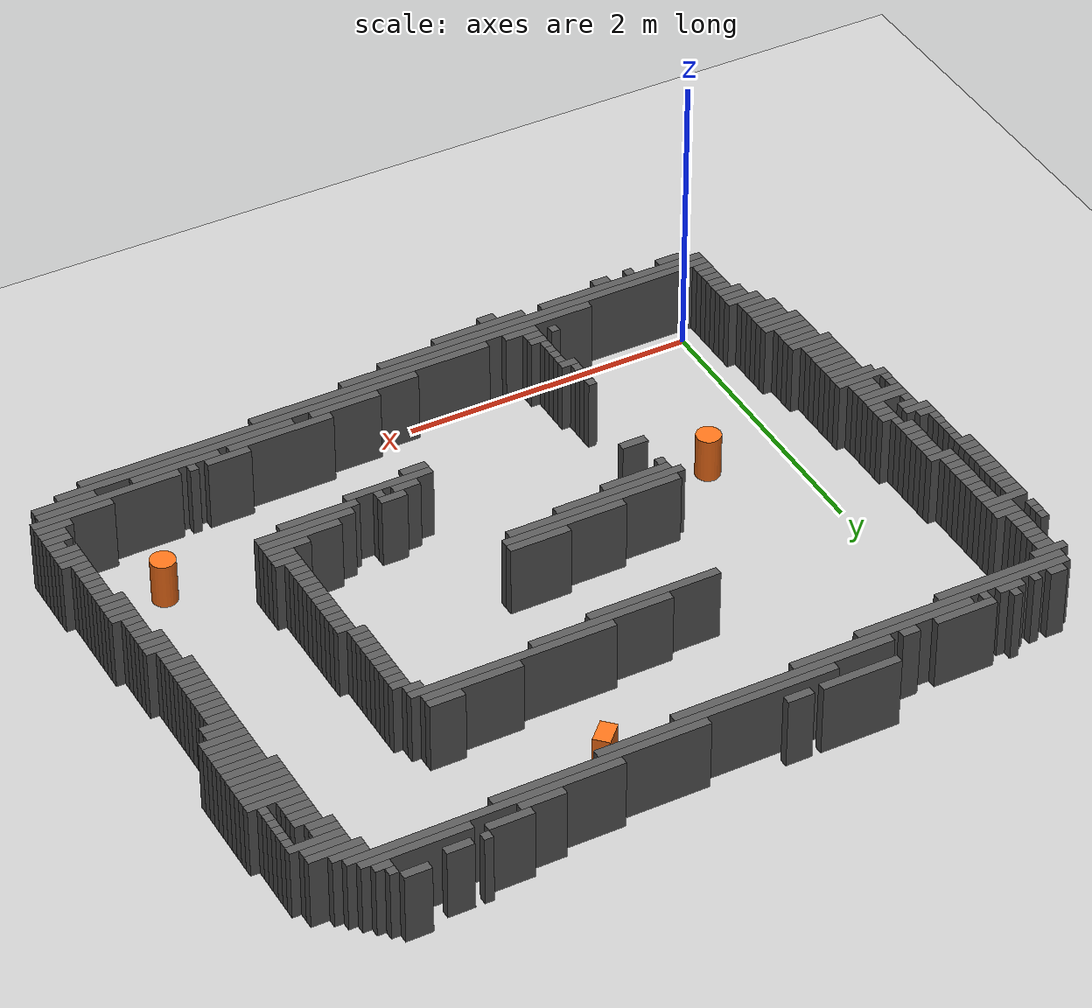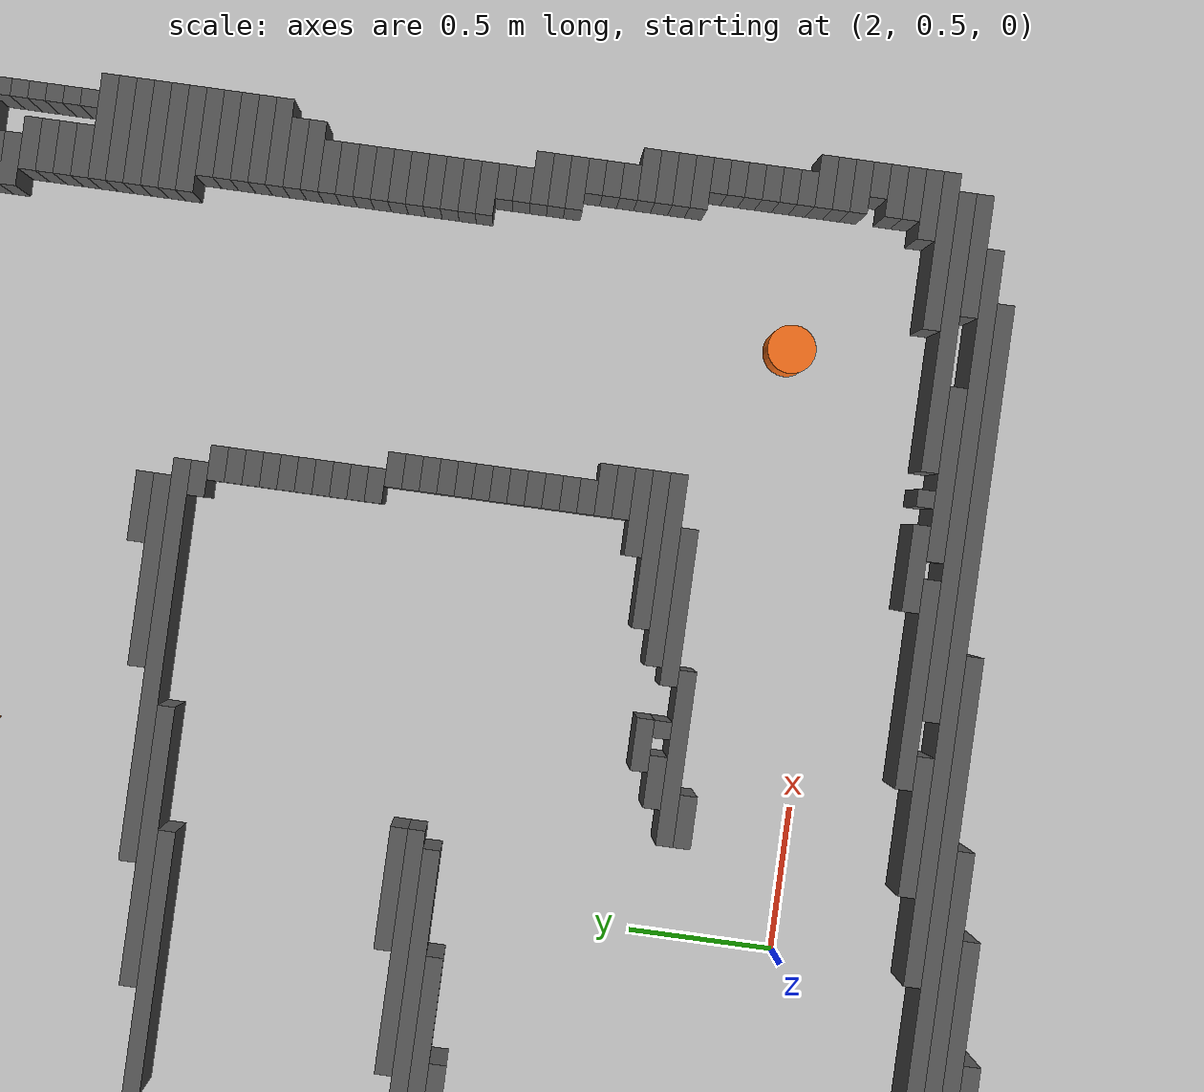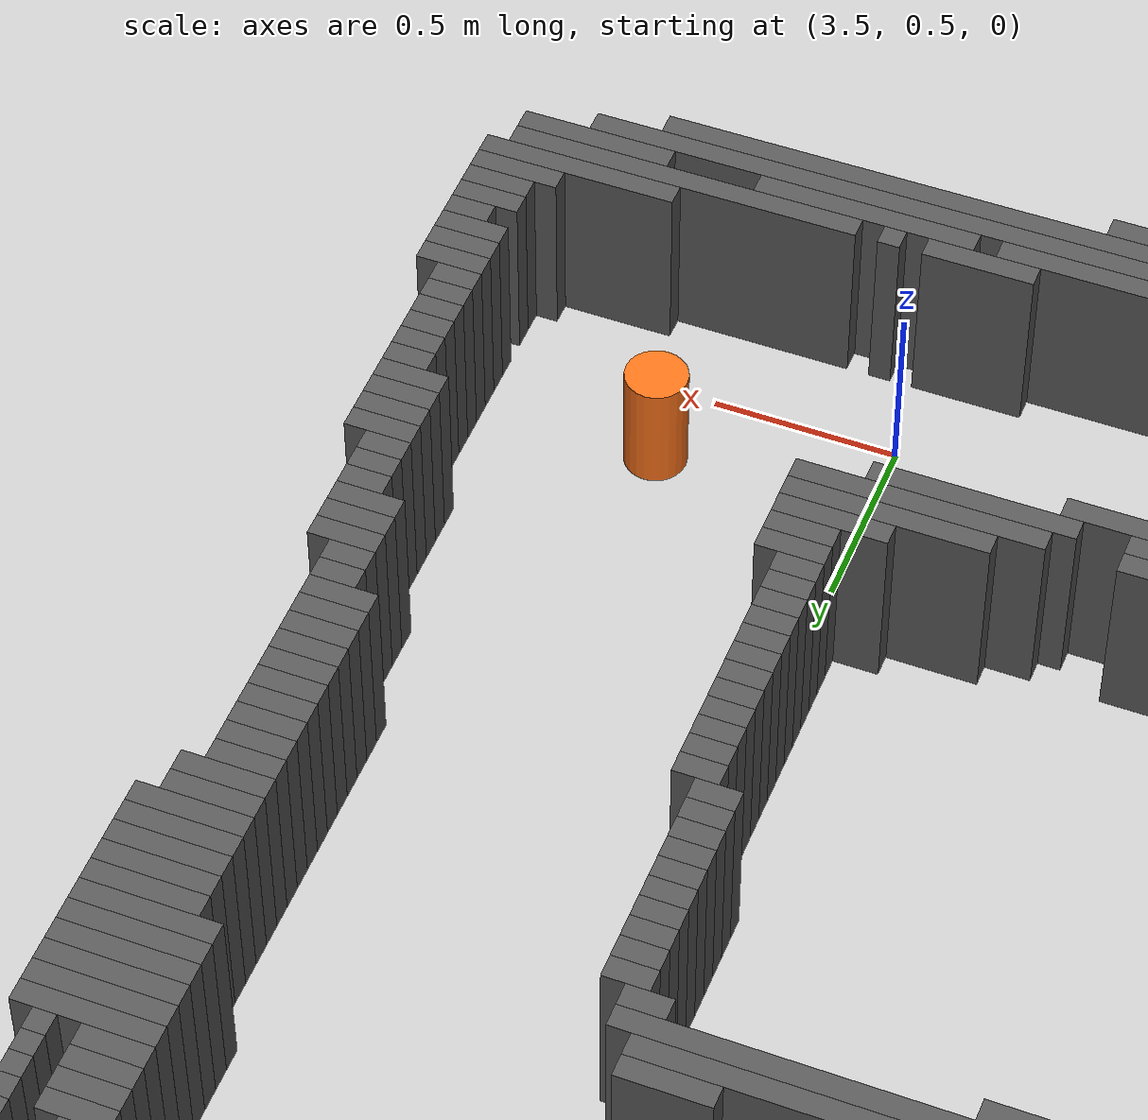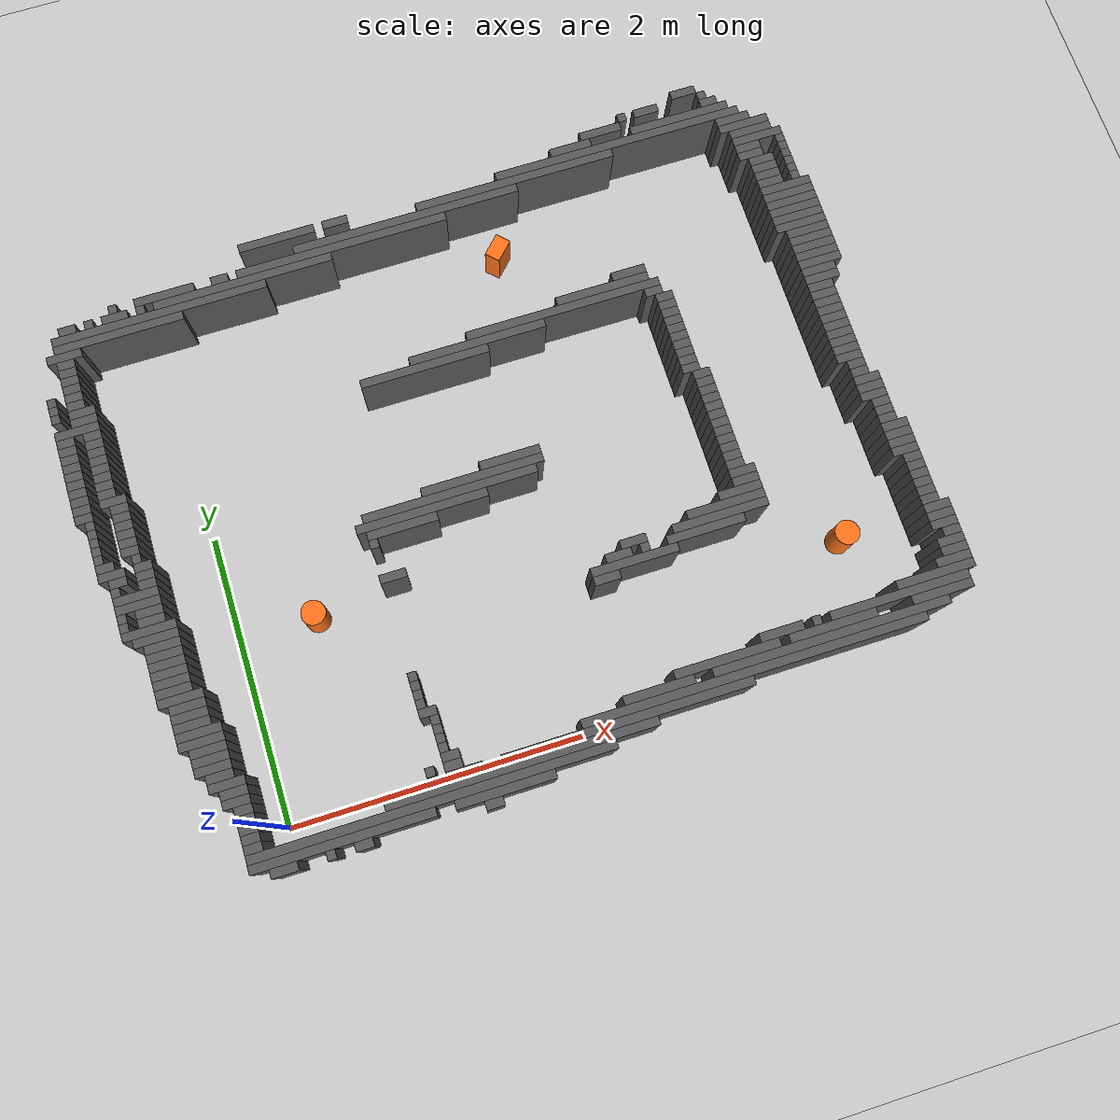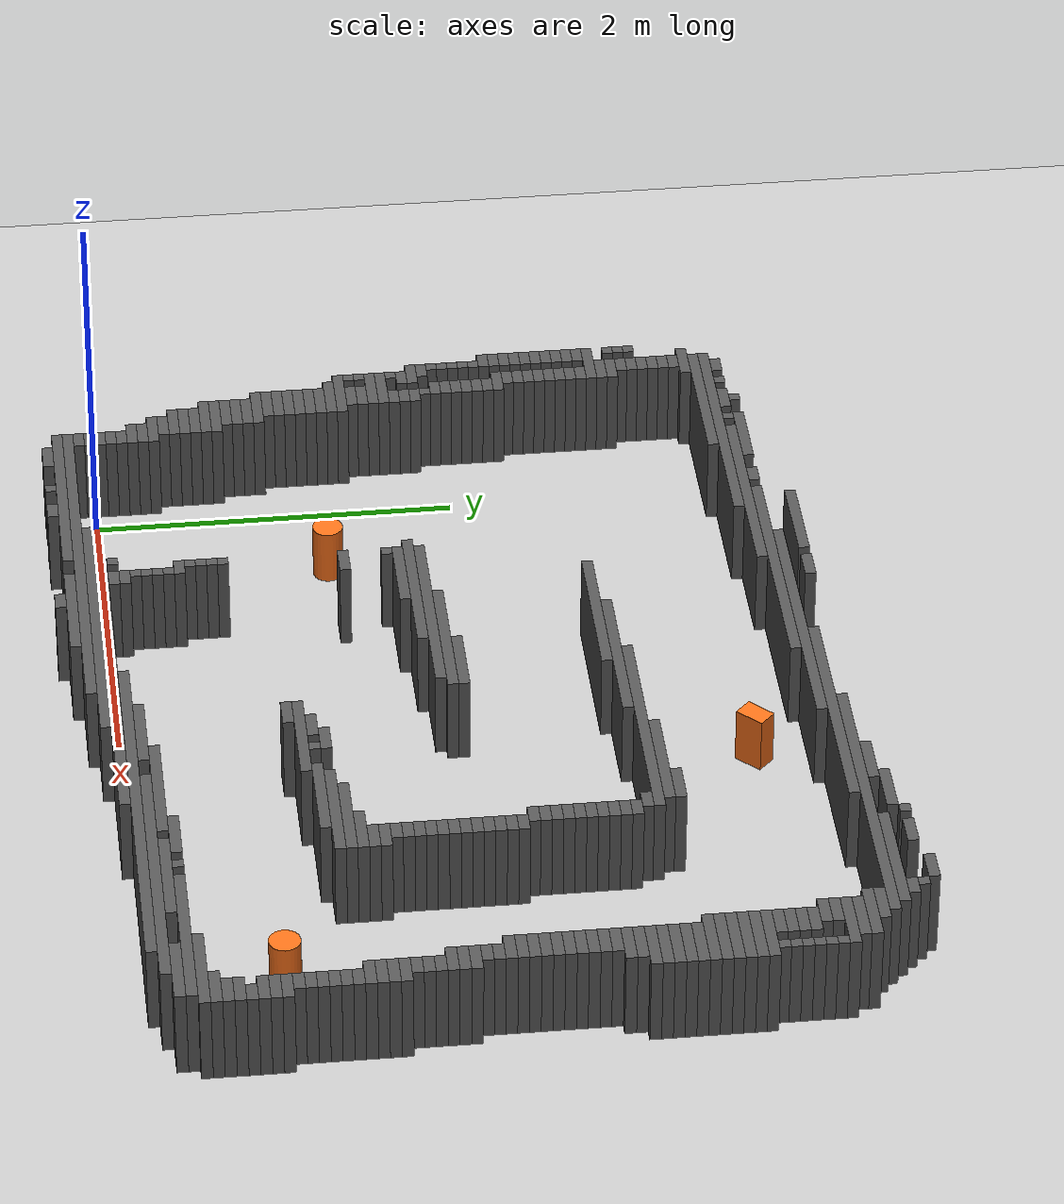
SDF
<?xml version='1.0'?>
<sdf version='1.6'>
  <world name='my_map'>
    <include><uri>model://sun</uri></include>
    <model name='ground_plane'>
      <static>true</static>
      <link name='link'>
        <collision name='collision'><geometry><plane><normal>0 0 1</normal><size>20 20</size></plane></geometry></collision>
        <visual name='visual'><geometry><plane><normal>0 0 1</normal><size>20 20</size></plane></geometry><material><script><uri>file://media/materials/scripts/gazebo.material</uri><name>Gazebo/Grey</name></script></material></visual>
      </link>
    </model>
    <model name='my_map_walls'>
      <static>true</static>
      <link name='wall_000'>
        <pose>4.0500 4.0620 0.2500 0 0 0</pose>
        <collision name='collision'><geometry><box><size>0.1800 0.0600 0.5000</size></box></geometry></collision>
        <visual name='visual'><geometry><box><size>0.1800 0.0600 0.5000</size></box></geometry><material><ambient>0.25 0.25 0.25 1</ambient><diffuse>0.35 0.35 0.35 1</diffuse></material></visual>
      </link>
      <link name='wall_001'>
        <pose>3.5700 4.0020 0.2500 0 0 0</pose>
        <collision name='collision'><geometry><box><size>0.0600 0.0600 0.5000</size></box></geometry></collision>
        <visual name='visual'><geometry><box><size>0.0600 0.0600 0.5000</size></box></geometry><material><ambient>0.25 0.25 0.25 1</ambient><diffuse>0.35 0.35 0.35 1</diffuse></material></visual>
      </link>
      <link name='wall_002'>
        <pose>3.7500 4.0020 0.2500 0 0 0</pose>
        <collision name='collision'><geometry><box><size>0.1800 0.0600 0.5000</size></box></geometry></collision>
        <visual name='visual'><geometry><box><size>0.1800 0.0600 0.5000</size></box></geometry><material><ambient>0.25 0.25 0.25 1</ambient><diffuse>0.35 0.35 0.35 1</diffuse></material></visual>
      </link>
      <link name='wall_003'>
        <pose>4.1700 4.0020 0.2500 0 0 0</pose>
        <collision name='collision'><geometry><box><size>0.0600 0.0600 0.5000</size></box></geometry></collision>
        <visual name='visual'><geometry><box><size>0.0600 0.0600 0.5000</size></box></geometry><material><ambient>0.25 0.25 0.25 1</ambient><diffuse>0.35 0.35 0.35 1</diffuse></material></visual>
      </link>
      <link name='wall_004'>
        <pose>3.3900 3.9420 0.2500 0 0 0</pose>
        <collision name='collision'><geometry><box><size>0.3000 0.0600 0.5000</size></box></geometry></collision>
        <visual name='visual'><geometry><box><size>0.3000 0.0600 0.5000</size></box></geometry><material><ambient>0.25 0.25 0.25 1</ambient><diffuse>0.35 0.35 0.35 1</diffuse></material></visual>
      </link>
      <link name='wall_005'>
        <pose>4.2000 3.9420 0.2500 0 0 0</pose>
        <collision name='collision'><geometry><box><size>0.1200 0.0600 0.5000</size></box></geometry></collision>
        <visual name='visual'><geometry><box><size>0.1200 0.0600 0.5000</size></box></geometry><material><ambient>0.25 0.25 0.25 1</ambient><diffuse>0.35 0.35 0.35 1</diffuse></material></visual>
      </link>
      <link name='wall_006'>
        <pose>3.1500 3.8820 0.2500 0 0 0</pose>
        <collision name='collision'><geometry><box><size>0.3000 0.0600 0.5000</size></box></geometry></collision>
        <visual name='visual'><geometry><box><size>0.3000 0.0600 0.5000</size></box></geometry><material><ambient>0.25 0.25 0.25 1</ambient><diffuse>0.35 0.35 0.35 1</diffuse></material></visual>
      </link>
      <link name='wall_007'>
        <pose>3.9600 3.8820 0.2500 0 0 0</pose>
        <collision name='collision'><geometry><box><size>0.7200 0.0600 0.5000</size></box></geometry></collision>
        <visual name='visual'><geometry><box><size>0.7200 0.0600 0.5000</size></box></geometry><material><ambient>0.25 0.25 0.25 1</ambient><diffuse>0.35 0.35 0.35 1</diffuse></material></visual>
      </link>
      <link name='wall_008'>
        <pose>0.9900 3.8220 0.2500 0 0 0</pose>
        <collision name='collision'><geometry><box><size>0.5400 0.0600 0.5000</size></box></geometry></collision>
        <visual name='visual'><geometry><box><size>0.5400 0.0600 0.5000</size></box></geometry><material><ambient>0.25 0.25 0.25 1</ambient><diffuse>0.35 0.35 0.35 1</diffuse></material></visual>
      </link>
      <link name='wall_009'>
        <pose>1.4100 3.8220 0.2500 0 0 0</pose>
        <collision name='collision'><geometry><box><size>0.1800 0.0600 0.5000</size></box></geometry></collision>
        <visual name='visual'><geometry><box><size>0.1800 0.0600 0.5000</size></box></geometry><material><ambient>0.25 0.25 0.25 1</ambient><diffuse>0.35 0.35 0.35 1</diffuse></material></visual>
      </link>
      <link name='wall_010'>
        <pose>3.4800 3.8220 0.2500 0 0 0</pose>
        <collision name='collision'><geometry><box><size>1.8000 0.0600 0.5000</size></box></geometry></collision>
        <visual name='visual'><geometry><box><size>1.8000 0.0600 0.5000</size></box></geometry><material><ambient>0.25 0.25 0.25 1</ambient><diffuse>0.35 0.35 0.35 1</diffuse></material></visual>
      </link>
      <link name='wall_011'>
        <pose>2.7000 3.7620 0.2500 0 0 0</pose>
        <collision name='collision'><geometry><box><size>1.4400 0.0600 0.5000</size></box></geometry></collision>
        <visual name='visual'><geometry><box><size>1.4400 0.0600 0.5000</size></box></geometry><material><ambient>0.25 0.25 0.25 1</ambient><diffuse>0.35 0.35 0.35 1</diffuse></material></visual>
      </link>
      <link name='wall_012'>
        <pose>4.3200 3.7620 0.2500 0 0 0</pose>
        <collision name='collision'><geometry><box><size>0.2400 0.0600 0.5000</size></box></geometry></collision>
        <visual name='visual'><geometry><box><size>0.2400 0.0600 0.5000</size></box></geometry><material><ambient>0.25 0.25 0.25 1</ambient><diffuse>0.35 0.35 0.35 1</diffuse></material></visual>
      </link>
      <link name='wall_013'>
        <pose>1.8900 3.7020 0.2500 0 0 0</pose>
        <collision name='collision'><geometry><box><size>1.6200 0.0600 0.5000</size></box></geometry></collision>
        <visual name='visual'><geometry><box><size>1.6200 0.0600 0.5000</size></box></geometry><material><ambient>0.25 0.25 0.25 1</ambient><diffuse>0.35 0.35 0.35 1</diffuse></material></visual>
      </link>
      <link name='wall_014'>
        <pose>4.3800 3.7020 0.2500 0 0 0</pose>
        <collision name='collision'><geometry><box><size>0.3600 0.0600 0.5000</size></box></geometry></collision>
        <visual name='visual'><geometry><box><size>0.3600 0.0600 0.5000</size></box></geometry><material><ambient>0.25 0.25 0.25 1</ambient><diffuse>0.35 0.35 0.35 1</diffuse></material></visual>
      </link>
      <link name='wall_015'>
        <pose>-0.2100 3.6420 0.2500 0 0 0</pose>
        <collision name='collision'><geometry><box><size>0.0600 0.0600 0.5000</size></box></geometry></collision>
        <visual name='visual'><geometry><box><size>0.0600 0.0600 0.5000</size></box></geometry><material><ambient>0.25 0.25 0.25 1</ambient><diffuse>0.35 0.35 0.35 1</diffuse></material></visual>
      </link>
      <link name='wall_016'>
        <pose>0.1500 3.6420 0.2500 0 0 0</pose>
        <collision name='collision'><geometry><box><size>0.4200 0.0600 0.5000</size></box></geometry></collision>
        <visual name='visual'><geometry><box><size>0.4200 0.0600 0.5000</size></box></geometry><material><ambient>0.25 0.25 0.25 1</ambient><diffuse>0.35 0.35 0.35 1</diffuse></material></visual>
      </link>
      <link name='wall_017'>
        <pose>0.5400 3.6420 0.2500 0 0 0</pose>
        <collision name='collision'><geometry><box><size>0.1200 0.0600 0.5000</size></box></geometry></collision>
        <visual name='visual'><geometry><box><size>0.1200 0.0600 0.5000</size></box></geometry><material><ambient>0.25 0.25 0.25 1</ambient><diffuse>0.35 0.35 0.35 1</diffuse></material></visual>
      </link>
      <link name='wall_018'>
        <pose>1.4100 3.6420 0.2500 0 0 0</pose>
        <collision name='collision'><geometry><box><size>1.5000 0.0600 0.5000</size></box></geometry></collision>
        <visual name='visual'><geometry><box><size>1.5000 0.0600 0.5000</size></box></geometry><material><ambient>0.25 0.25 0.25 1</ambient><diffuse>0.35 0.35 0.35 1</diffuse></material></visual>
      </link>
      <link name='wall_019'>
        <pose>4.4100 3.6420 0.2500 0 0 0</pose>
        <collision name='collision'><geometry><box><size>0.3000 0.0600 0.5000</size></box></geometry></collision>
        <visual name='visual'><geometry><box><size>0.3000 0.0600 0.5000</size></box></geometry><material><ambient>0.25 0.25 0.25 1</ambient><diffuse>0.35 0.35 0.35 1</diffuse></material></visual>
      </link>
      <link name='wall_020'>
        <pose>-0.5400 3.5820 0.2500 0 0 0</pose>
        <collision name='collision'><geometry><box><size>0.1200 0.0600 0.5000</size></box></geometry></collision>
        <visual name='visual'><geometry><box><size>0.1200 0.0600 0.5000</size></box></geometry><material><ambient>0.25 0.25 0.25 1</ambient><diffuse>0.35 0.35 0.35 1</diffuse></material></visual>
      </link>
      <link name='wall_021'>
        <pose>-0.3900 3.5820 0.2500 0 0 0</pose>
        <collision name='collision'><geometry><box><size>0.0600 0.0600 0.5000</size></box></geometry></collision>
        <visual name='visual'><geometry><box><size>0.0600 0.0600 0.5000</size></box></geometry><material><ambient>0.25 0.25 0.25 1</ambient><diffuse>0.35 0.35 0.35 1</diffuse></material></visual>
      </link>
      <link name='wall_022'>
        <pose>-0.2100 3.5820 0.2500 0 0 0</pose>
        <collision name='collision'><geometry><box><size>0.1800 0.0600 0.5000</size></box></geometry></collision>
        <visual name='visual'><geometry><box><size>0.1800 0.0600 0.5000</size></box></geometry><material><ambient>0.25 0.25 0.25 1</ambient><diffuse>0.35 0.35 0.35 1</diffuse></material></visual>
      </link>
      <link name='wall_023'>
        <pose>-0.0300 3.5820 0.2500 0 0 0</pose>
        <collision name='collision'><geometry><box><size>0.0600 0.0600 0.5000</size></box></geometry></collision>
        <visual name='visual'><geometry><box><size>0.0600 0.0600 0.5000</size></box></geometry><material><ambient>0.25 0.25 0.25 1</ambient><diffuse>0.35 0.35 0.35 1</diffuse></material></visual>
      </link>
      <link name='wall_024'>
        <pose>0.6900 3.5820 0.2500 0 0 0</pose>
        <collision name='collision'><geometry><box><size>1.2600 0.0600 0.5000</size></box></geometry></collision>
        <visual name='visual'><geometry><box><size>1.2600 0.0600 0.5000</size></box></geometry><material><ambient>0.25 0.25 0.25 1</ambient><diffuse>0.35 0.35 0.35 1</diffuse></material></visual>
      </link>
      <link name='wall_025'>
        <pose>4.4400 3.5820 0.2500 0 0 0</pose>
        <collision name='collision'><geometry><box><size>0.3600 0.0600 0.5000</size></box></geometry></collision>
        <visual name='visual'><geometry><box><size>0.3600 0.0600 0.5000</size></box></geometry><material><ambient>0.25 0.25 0.25 1</ambient><diffuse>0.35 0.35 0.35 1</diffuse></material></visual>
      </link>
      <link name='wall_026'>
        <pose>0.0900 3.5220 0.2500 0 0 0</pose>
        <collision name='collision'><geometry><box><size>1.5000 0.0600 0.5000</size></box></geometry></collision>
        <visual name='visual'><geometry><box><size>1.5000 0.0600 0.5000</size></box></geometry><material><ambient>0.25 0.25 0.25 1</ambient><diffuse>0.35 0.35 0.35 1</diffuse></material></visual>
      </link>
      <link name='wall_027'>
        <pose>4.3500 3.5220 0.2500 0 0 0</pose>
        <collision name='collision'><geometry><box><size>0.1800 0.0600 0.5000</size></box></geometry></collision>
        <visual name='visual'><geometry><box><size>0.1800 0.0600 0.5000</size></box></geometry><material><ambient>0.25 0.25 0.25 1</ambient><diffuse>0.35 0.35 0.35 1</diffuse></material></visual>
      </link>
      <link name='wall_028'>
        <pose>4.5900 3.5220 0.2500 0 0 0</pose>
        <collision name='collision'><geometry><box><size>0.0600 0.0600 0.5000</size></box></geometry></collision>
        <visual name='visual'><geometry><box><size>0.0600 0.0600 0.5000</size></box></geometry><material><ambient>0.25 0.25 0.25 1</ambient><diffuse>0.35 0.35 0.35 1</diffuse></material></visual>
      </link>
      <link name='wall_029'>
        <pose>-0.2100 3.4620 0.2500 0 0 0</pose>
        <collision name='collision'><geometry><box><size>0.9000 0.0600 0.5000</size></box></geometry></collision>
        <visual name='visual'><geometry><box><size>0.9000 0.0600 0.5000</size></box></geometry><material><ambient>0.25 0.25 0.25 1</ambient><diffuse>0.35 0.35 0.35 1</diffuse></material></visual>
      </link>
      <link name='wall_030'>
        <pose>4.3500 3.4620 0.2500 0 0 0</pose>
        <collision name='collision'><geometry><box><size>0.1800 0.0600 0.5000</size></box></geometry></collision>
        <visual name='visual'><geometry><box><size>0.1800 0.0600 0.5000</size></box></geometry><material><ambient>0.25 0.25 0.25 1</ambient><diffuse>0.35 0.35 0.35 1</diffuse></material></visual>
      </link>
      <link name='wall_031'>
        <pose>4.5900 3.4620 0.2500 0 0 0</pose>
        <collision name='collision'><geometry><box><size>0.0600 0.0600 0.5000</size></box></geometry></collision>
        <visual name='visual'><geometry><box><size>0.0600 0.0600 0.5000</size></box></geometry><material><ambient>0.25 0.25 0.25 1</ambient><diffuse>0.35 0.35 0.35 1</diffuse></material></visual>
      </link>
      <link name='wall_032'>
        <pose>-0.6000 3.4020 0.2500 0 0 0</pose>
        <collision name='collision'><geometry><box><size>0.2400 0.0600 0.5000</size></box></geometry></collision>
        <visual name='visual'><geometry><box><size>0.2400 0.0600 0.5000</size></box></geometry><material><ambient>0.25 0.25 0.25 1</ambient><diffuse>0.35 0.35 0.35 1</diffuse></material></visual>
      </link>
      <link name='wall_033'>
        <pose>4.4100 3.4020 0.2500 0 0 0</pose>
        <collision name='collision'><geometry><box><size>0.1800 0.0600 0.5000</size></box></geometry></collision>
        <visual name='visual'><geometry><box><size>0.1800 0.0600 0.5000</size></box></geometry><material><ambient>0.25 0.25 0.25 1</ambient><diffuse>0.35 0.35 0.35 1</diffuse></material></visual>
      </link>
      <link name='wall_034'>
        <pose>4.5900 3.4020 0.2500 0 0 0</pose>
        <collision name='collision'><geometry><box><size>0.0600 0.0600 0.5000</size></box></geometry></collision>
        <visual name='visual'><geometry><box><size>0.0600 0.0600 0.5000</size></box></geometry><material><ambient>0.25 0.25 0.25 1</ambient><diffuse>0.35 0.35 0.35 1</diffuse></material></visual>
      </link>
      <link name='wall_035'>
        <pose>-0.6000 3.3420 0.2500 0 0 0</pose>
        <collision name='collision'><geometry><box><size>0.1200 0.0600 0.5000</size></box></geometry></collision>
        <visual name='visual'><geometry><box><size>0.1200 0.0600 0.5000</size></box></geometry><material><ambient>0.25 0.25 0.25 1</ambient><diffuse>0.35 0.35 0.35 1</diffuse></material></visual>
      </link>
      <link name='wall_036'>
        <pose>4.4100 3.3420 0.2500 0 0 0</pose>
        <collision name='collision'><geometry><box><size>0.1800 0.0600 0.5000</size></box></geometry></collision>
        <visual name='visual'><geometry><box><size>0.1800 0.0600 0.5000</size></box></geometry><material><ambient>0.25 0.25 0.25 1</ambient><diffuse>0.35 0.35 0.35 1</diffuse></material></visual>
      </link>
      <link name='wall_037'>
        <pose>4.5900 3.3420 0.2500 0 0 0</pose>
        <collision name='collision'><geometry><box><size>0.0600 0.0600 0.5000</size></box></geometry></collision>
        <visual name='visual'><geometry><box><size>0.0600 0.0600 0.5000</size></box></geometry><material><ambient>0.25 0.25 0.25 1</ambient><diffuse>0.35 0.35 0.35 1</diffuse></material></visual>
      </link>
      <link name='wall_038'>
        <pose>-0.6000 3.2820 0.2500 0 0 0</pose>
        <collision name='collision'><geometry><box><size>0.1200 0.0600 0.5000</size></box></geometry></collision>
        <visual name='visual'><geometry><box><size>0.1200 0.0600 0.5000</size></box></geometry><material><ambient>0.25 0.25 0.25 1</ambient><diffuse>0.35 0.35 0.35 1</diffuse></material></visual>
      </link>
      <link name='wall_039'>
        <pose>4.4100 3.2820 0.2500 0 0 0</pose>
        <collision name='collision'><geometry><box><size>0.1800 0.0600 0.5000</size></box></geometry></collision>
        <visual name='visual'><geometry><box><size>0.1800 0.0600 0.5000</size></box></geometry><material><ambient>0.25 0.25 0.25 1</ambient><diffuse>0.35 0.35 0.35 1</diffuse></material></visual>
      </link>
      <link name='wall_040'>
        <pose>4.5900 3.2820 0.2500 0 0 0</pose>
        <collision name='collision'><geometry><box><size>0.0600 0.0600 0.5000</size></box></geometry></collision>
        <visual name='visual'><geometry><box><size>0.0600 0.0600 0.5000</size></box></geometry><material><ambient>0.25 0.25 0.25 1</ambient><diffuse>0.35 0.35 0.35 1</diffuse></material></visual>
      </link>
      <link name='wall_041'>
        <pose>-0.6000 3.2220 0.2500 0 0 0</pose>
        <collision name='collision'><geometry><box><size>0.1200 0.0600 0.5000</size></box></geometry></collision>
        <visual name='visual'><geometry><box><size>0.1200 0.0600 0.5000</size></box></geometry><material><ambient>0.25 0.25 0.25 1</ambient><diffuse>0.35 0.35 0.35 1</diffuse></material></visual>
      </link>
      <link name='wall_042'>
        <pose>4.4100 3.2220 0.2500 0 0 0</pose>
        <collision name='collision'><geometry><box><size>0.1800 0.0600 0.5000</size></box></geometry></collision>
        <visual name='visual'><geometry><box><size>0.1800 0.0600 0.5000</size></box></geometry><material><ambient>0.25 0.25 0.25 1</ambient><diffuse>0.35 0.35 0.35 1</diffuse></material></visual>
      </link>
      <link name='wall_043'>
        <pose>4.5900 3.2220 0.2500 0 0 0</pose>
        <collision name='collision'><geometry><box><size>0.0600 0.0600 0.5000</size></box></geometry></collision>
        <visual name='visual'><geometry><box><size>0.0600 0.0600 0.5000</size></box></geometry><material><ambient>0.25 0.25 0.25 1</ambient><diffuse>0.35 0.35 0.35 1</diffuse></material></visual>
      </link>
      <link name='wall_044'>
        <pose>-0.6000 3.1620 0.2500 0 0 0</pose>
        <collision name='collision'><geometry><box><size>0.1200 0.0600 0.5000</size></box></geometry></collision>
        <visual name='visual'><geometry><box><size>0.1200 0.0600 0.5000</size></box></geometry><material><ambient>0.25 0.25 0.25 1</ambient><diffuse>0.35 0.35 0.35 1</diffuse></material></visual>
      </link>
      <link name='wall_045'>
        <pose>4.5000 3.1620 0.2500 0 0 0</pose>
        <collision name='collision'><geometry><box><size>0.3600 0.0600 0.5000</size></box></geometry></collision>
        <visual name='visual'><geometry><box><size>0.3600 0.0600 0.5000</size></box></geometry><material><ambient>0.25 0.25 0.25 1</ambient><diffuse>0.35 0.35 0.35 1</diffuse></material></visual>
      </link>
      <link name='wall_046'>
        <pose>-0.7500 3.1020 0.2500 0 0 0</pose>
        <collision name='collision'><geometry><box><size>0.0600 0.0600 0.5000</size></box></geometry></collision>
        <visual name='visual'><geometry><box><size>0.0600 0.0600 0.5000</size></box></geometry><material><ambient>0.25 0.25 0.25 1</ambient><diffuse>0.35 0.35 0.35 1</diffuse></material></visual>
      </link>
      <link name='wall_047'>
        <pose>-0.6000 3.1020 0.2500 0 0 0</pose>
        <collision name='collision'><geometry><box><size>0.1200 0.0600 0.5000</size></box></geometry></collision>
        <visual name='visual'><geometry><box><size>0.1200 0.0600 0.5000</size></box></geometry><material><ambient>0.25 0.25 0.25 1</ambient><diffuse>0.35 0.35 0.35 1</diffuse></material></visual>
      </link>
      <link name='wall_048'>
        <pose>4.5000 3.1020 0.2500 0 0 0</pose>
        <collision name='collision'><geometry><box><size>0.3600 0.0600 0.5000</size></box></geometry></collision>
        <visual name='visual'><geometry><box><size>0.3600 0.0600 0.5000</size></box></geometry><material><ambient>0.25 0.25 0.25 1</ambient><diffuse>0.35 0.35 0.35 1</diffuse></material></visual>
      </link>
      <link name='wall_049'>
        <pose>-0.7500 3.0420 0.2500 0 0 0</pose>
        <collision name='collision'><geometry><box><size>0.0600 0.0600 0.5000</size></box></geometry></collision>
        <visual name='visual'><geometry><box><size>0.0600 0.0600 0.5000</size></box></geometry><material><ambient>0.25 0.25 0.25 1</ambient><diffuse>0.35 0.35 0.35 1</diffuse></material></visual>
      </link>
      <link name='wall_050'>
        <pose>-0.6000 3.0420 0.2500 0 0 0</pose>
        <collision name='collision'><geometry><box><size>0.1200 0.0600 0.5000</size></box></geometry></collision>
        <visual name='visual'><geometry><box><size>0.1200 0.0600 0.5000</size></box></geometry><material><ambient>0.25 0.25 0.25 1</ambient><diffuse>0.35 0.35 0.35 1</diffuse></material></visual>
      </link>
      <link name='wall_051'>
        <pose>4.5000 3.0420 0.2500 0 0 0</pose>
        <collision name='collision'><geometry><box><size>0.3600 0.0600 0.5000</size></box></geometry></collision>
        <visual name='visual'><geometry><box><size>0.3600 0.0600 0.5000</size></box></geometry><material><ambient>0.25 0.25 0.25 1</ambient><diffuse>0.35 0.35 0.35 1</diffuse></material></visual>
      </link>
      <link name='wall_052'>
        <pose>-0.7500 2.9820 0.2500 0 0 0</pose>
        <collision name='collision'><geometry><box><size>0.0600 0.0600 0.5000</size></box></geometry></collision>
        <visual name='visual'><geometry><box><size>0.0600 0.0600 0.5000</size></box></geometry><material><ambient>0.25 0.25 0.25 1</ambient><diffuse>0.35 0.35 0.35 1</diffuse></material></visual>
      </link>
      <link name='wall_053'>
        <pose>-0.5700 2.9820 0.2500 0 0 0</pose>
        <collision name='collision'><geometry><box><size>0.1800 0.0600 0.5000</size></box></geometry></collision>
        <visual name='visual'><geometry><box><size>0.1800 0.0600 0.5000</size></box></geometry><material><ambient>0.25 0.25 0.25 1</ambient><diffuse>0.35 0.35 0.35 1</diffuse></material></visual>
      </link>
      <link name='wall_054'>
        <pose>4.5000 2.9820 0.2500 0 0 0</pose>
        <collision name='collision'><geometry><box><size>0.3600 0.0600 0.5000</size></box></geometry></collision>
        <visual name='visual'><geometry><box><size>0.3600 0.0600 0.5000</size></box></geometry><material><ambient>0.25 0.25 0.25 1</ambient><diffuse>0.35 0.35 0.35 1</diffuse></material></visual>
      </link>
      <link name='wall_055'>
        <pose>-0.5700 2.9220 0.2500 0 0 0</pose>
        <collision name='collision'><geometry><box><size>0.1800 0.0600 0.5000</size></box></geometry></collision>
        <visual name='visual'><geometry><box><size>0.1800 0.0600 0.5000</size></box></geometry><material><ambient>0.25 0.25 0.25 1</ambient><diffuse>0.35 0.35 0.35 1</diffuse></material></visual>
      </link>
      <link name='wall_056'>
        <pose>4.5000 2.9220 0.2500 0 0 0</pose>
        <collision name='collision'><geometry><box><size>0.3600 0.0600 0.5000</size></box></geometry></collision>
        <visual name='visual'><geometry><box><size>0.3600 0.0600 0.5000</size></box></geometry><material><ambient>0.25 0.25 0.25 1</ambient><diffuse>0.35 0.35 0.35 1</diffuse></material></visual>
      </link>
      <link name='wall_057'>
        <pose>-0.6300 2.8620 0.2500 0 0 0</pose>
        <collision name='collision'><geometry><box><size>0.3000 0.0600 0.5000</size></box></geometry></collision>
        <visual name='visual'><geometry><box><size>0.3000 0.0600 0.5000</size></box></geometry><material><ambient>0.25 0.25 0.25 1</ambient><diffuse>0.35 0.35 0.35 1</diffuse></material></visual>
      </link>
      <link name='wall_058'>
        <pose>3.2400 2.8620 0.2500 0 0 0</pose>
        <collision name='collision'><geometry><box><size>0.2400 0.0600 0.5000</size></box></geometry></collision>
        <visual name='visual'><geometry><box><size>0.2400 0.0600 0.5000</size></box></geometry><material><ambient>0.25 0.25 0.25 1</ambient><diffuse>0.35 0.35 0.35 1</diffuse></material></visual>
      </link>
      <link name='wall_059'>
        <pose>4.5000 2.8620 0.2500 0 0 0</pose>
        <collision name='collision'><geometry><box><size>0.3600 0.0600 0.5000</size></box></geometry></collision>
        <visual name='visual'><geometry><box><size>0.3600 0.0600 0.5000</size></box></geometry><material><ambient>0.25 0.25 0.25 1</ambient><diffuse>0.35 0.35 0.35 1</diffuse></material></visual>
      </link>
      <link name='wall_060'>
        <pose>-0.7200 2.8020 0.2500 0 0 0</pose>
        <collision name='collision'><geometry><box><size>0.1200 0.0600 0.5000</size></box></geometry></collision>
        <visual name='visual'><geometry><box><size>0.1200 0.0600 0.5000</size></box></geometry><material><ambient>0.25 0.25 0.25 1</ambient><diffuse>0.35 0.35 0.35 1</diffuse></material></visual>
      </link>
      <link name='wall_061'>
        <pose>-0.5400 2.8020 0.2500 0 0 0</pose>
        <collision name='collision'><geometry><box><size>0.1200 0.0600 0.5000</size></box></geometry></collision>
        <visual name='visual'><geometry><box><size>0.1200 0.0600 0.5000</size></box></geometry><material><ambient>0.25 0.25 0.25 1</ambient><diffuse>0.35 0.35 0.35 1</diffuse></material></visual>
      </link>
      <link name='wall_062'>
        <pose>3.0300 2.8020 0.2500 0 0 0</pose>
        <collision name='collision'><geometry><box><size>0.6600 0.0600 0.5000</size></box></geometry></collision>
        <visual name='visual'><geometry><box><size>0.6600 0.0600 0.5000</size></box></geometry><material><ambient>0.25 0.25 0.25 1</ambient><diffuse>0.35 0.35 0.35 1</diffuse></material></visual>
      </link>
      <link name='wall_063'>
        <pose>4.5300 2.8020 0.2500 0 0 0</pose>
        <collision name='collision'><geometry><box><size>0.3000 0.0600 0.5000</size></box></geometry></collision>
        <visual name='visual'><geometry><box><size>0.3000 0.0600 0.5000</size></box></geometry><material><ambient>0.25 0.25 0.25 1</ambient><diffuse>0.35 0.35 0.35 1</diffuse></material></visual>
      </link>
      <link name='wall_064'>
        <pose>-0.7200 2.7420 0.2500 0 0 0</pose>
        <collision name='collision'><geometry><box><size>0.1200 0.0600 0.5000</size></box></geometry></collision>
        <visual name='visual'><geometry><box><size>0.1200 0.0600 0.5000</size></box></geometry><material><ambient>0.25 0.25 0.25 1</ambient><diffuse>0.35 0.35 0.35 1</diffuse></material></visual>
      </link>
      <link name='wall_065'>
        <pose>-0.5400 2.7420 0.2500 0 0 0</pose>
        <collision name='collision'><geometry><box><size>0.1200 0.0600 0.5000</size></box></geometry></collision>
        <visual name='visual'><geometry><box><size>0.1200 0.0600 0.5000</size></box></geometry><material><ambient>0.25 0.25 0.25 1</ambient><diffuse>0.35 0.35 0.35 1</diffuse></material></visual>
      </link>
      <link name='wall_066'>
        <pose>2.7300 2.7420 0.2500 0 0 0</pose>
        <collision name='collision'><geometry><box><size>1.3800 0.0600 0.5000</size></box></geometry></collision>
        <visual name='visual'><geometry><box><size>1.3800 0.0600 0.5000</size></box></geometry><material><ambient>0.25 0.25 0.25 1</ambient><diffuse>0.35 0.35 0.35 1</diffuse></material></visual>
      </link>
      <link name='wall_067'>
        <pose>4.5300 2.7420 0.2500 0 0 0</pose>
        <collision name='collision'><geometry><box><size>0.3000 0.0600 0.5000</size></box></geometry></collision>
        <visual name='visual'><geometry><box><size>0.3000 0.0600 0.5000</size></box></geometry><material><ambient>0.25 0.25 0.25 1</ambient><diffuse>0.35 0.35 0.35 1</diffuse></material></visual>
      </link>
      <link name='wall_068'>
        <pose>-0.7200 2.6820 0.2500 0 0 0</pose>
        <collision name='collision'><geometry><box><size>0.1200 0.0600 0.5000</size></box></geometry></collision>
        <visual name='visual'><geometry><box><size>0.1200 0.0600 0.5000</size></box></geometry><material><ambient>0.25 0.25 0.25 1</ambient><diffuse>0.35 0.35 0.35 1</diffuse></material></visual>
      </link>
      <link name='wall_069'>
        <pose>-0.5400 2.6820 0.2500 0 0 0</pose>
        <collision name='collision'><geometry><box><size>0.1200 0.0600 0.5000</size></box></geometry></collision>
        <visual name='visual'><geometry><box><size>0.1200 0.0600 0.5000</size></box></geometry><material><ambient>0.25 0.25 0.25 1</ambient><diffuse>0.35 0.35 0.35 1</diffuse></material></visual>
      </link>
      <link name='wall_070'>
        <pose>2.1000 2.6820 0.2500 0 0 0</pose>
        <collision name='collision'><geometry><box><size>0.9600 0.0600 0.5000</size></box></geometry></collision>
        <visual name='visual'><geometry><box><size>0.9600 0.0600 0.5000</size></box></geometry><material><ambient>0.25 0.25 0.25 1</ambient><diffuse>0.35 0.35 0.35 1</diffuse></material></visual>
      </link>
      <link name='wall_071'>
        <pose>3.3600 2.6820 0.2500 0 0 0</pose>
        <collision name='collision'><geometry><box><size>0.1200 0.0600 0.5000</size></box></geometry></collision>
        <visual name='visual'><geometry><box><size>0.1200 0.0600 0.5000</size></box></geometry><material><ambient>0.25 0.25 0.25 1</ambient><diffuse>0.35 0.35 0.35 1</diffuse></material></visual>
      </link>
      <link name='wall_072'>
        <pose>4.5300 2.6820 0.2500 0 0 0</pose>
        <collision name='collision'><geometry><box><size>0.3000 0.0600 0.5000</size></box></geometry></collision>
        <visual name='visual'><geometry><box><size>0.3000 0.0600 0.5000</size></box></geometry><material><ambient>0.25 0.25 0.25 1</ambient><diffuse>0.35 0.35 0.35 1</diffuse></material></visual>
      </link>
      <link name='wall_073'>
        <pose>-0.7200 2.6220 0.2500 0 0 0</pose>
        <collision name='collision'><geometry><box><size>0.1200 0.0600 0.5000</size></box></geometry></collision>
        <visual name='visual'><geometry><box><size>0.1200 0.0600 0.5000</size></box></geometry><material><ambient>0.25 0.25 0.25 1</ambient><diffuse>0.35 0.35 0.35 1</diffuse></material></visual>
      </link>
      <link name='wall_074'>
        <pose>-0.5400 2.6220 0.2500 0 0 0</pose>
        <collision name='collision'><geometry><box><size>0.1200 0.0600 0.5000</size></box></geometry></collision>
        <visual name='visual'><geometry><box><size>0.1200 0.0600 0.5000</size></box></geometry><material><ambient>0.25 0.25 0.25 1</ambient><diffuse>0.35 0.35 0.35 1</diffuse></material></visual>
      </link>
      <link name='wall_075'>
        <pose>1.7100 2.6220 0.2500 0 0 0</pose>
        <collision name='collision'><geometry><box><size>0.9000 0.0600 0.5000</size></box></geometry></collision>
        <visual name='visual'><geometry><box><size>0.9000 0.0600 0.5000</size></box></geometry><material><ambient>0.25 0.25 0.25 1</ambient><diffuse>0.35 0.35 0.35 1</diffuse></material></visual>
      </link>
      <link name='wall_076'>
        <pose>3.4200 2.6220 0.2500 0 0 0</pose>
        <collision name='collision'><geometry><box><size>0.1200 0.0600 0.5000</size></box></geometry></collision>
        <visual name='visual'><geometry><box><size>0.1200 0.0600 0.5000</size></box></geometry><material><ambient>0.25 0.25 0.25 1</ambient><diffuse>0.35 0.35 0.35 1</diffuse></material></visual>
      </link>
      <link name='wall_077'>
        <pose>4.5300 2.6220 0.2500 0 0 0</pose>
        <collision name='collision'><geometry><box><size>0.3000 0.0600 0.5000</size></box></geometry></collision>
        <visual name='visual'><geometry><box><size>0.3000 0.0600 0.5000</size></box></geometry><material><ambient>0.25 0.25 0.25 1</ambient><diffuse>0.35 0.35 0.35 1</diffuse></material></visual>
      </link>
      <link name='wall_078'>
        <pose>-0.7200 2.5620 0.2500 0 0 0</pose>
        <collision name='collision'><geometry><box><size>0.1200 0.0600 0.5000</size></box></geometry></collision>
        <visual name='visual'><geometry><box><size>0.1200 0.0600 0.5000</size></box></geometry><material><ambient>0.25 0.25 0.25 1</ambient><diffuse>0.35 0.35 0.35 1</diffuse></material></visual>
      </link>
      <link name='wall_079'>
        <pose>-0.5400 2.5620 0.2500 0 0 0</pose>
        <collision name='collision'><geometry><box><size>0.1200 0.0600 0.5000</size></box></geometry></collision>
        <visual name='visual'><geometry><box><size>0.1200 0.0600 0.5000</size></box></geometry><material><ambient>0.25 0.25 0.25 1</ambient><diffuse>0.35 0.35 0.35 1</diffuse></material></visual>
      </link>
      <link name='wall_080'>
        <pose>3.4200 2.5620 0.2500 0 0 0</pose>
        <collision name='collision'><geometry><box><size>0.1200 0.0600 0.5000</size></box></geometry></collision>
        <visual name='visual'><geometry><box><size>0.1200 0.0600 0.5000</size></box></geometry><material><ambient>0.25 0.25 0.25 1</ambient><diffuse>0.35 0.35 0.35 1</diffuse></material></visual>
      </link>
      <link name='wall_081'>
        <pose>4.5300 2.5620 0.2500 0 0 0</pose>
        <collision name='collision'><geometry><box><size>0.3000 0.0600 0.5000</size></box></geometry></collision>
        <visual name='visual'><geometry><box><size>0.3000 0.0600 0.5000</size></box></geometry><material><ambient>0.25 0.25 0.25 1</ambient><diffuse>0.35 0.35 0.35 1</diffuse></material></visual>
      </link>
      <link name='wall_082'>
        <pose>-0.7200 2.5020 0.2500 0 0 0</pose>
        <collision name='collision'><geometry><box><size>0.1200 0.0600 0.5000</size></box></geometry></collision>
        <visual name='visual'><geometry><box><size>0.1200 0.0600 0.5000</size></box></geometry><material><ambient>0.25 0.25 0.25 1</ambient><diffuse>0.35 0.35 0.35 1</diffuse></material></visual>
      </link>
      <link name='wall_083'>
        <pose>-0.5400 2.5020 0.2500 0 0 0</pose>
        <collision name='collision'><geometry><box><size>0.1200 0.0600 0.5000</size></box></geometry></collision>
        <visual name='visual'><geometry><box><size>0.1200 0.0600 0.5000</size></box></geometry><material><ambient>0.25 0.25 0.25 1</ambient><diffuse>0.35 0.35 0.35 1</diffuse></material></visual>
      </link>
      <link name='wall_084'>
        <pose>3.4200 2.5020 0.2500 0 0 0</pose>
        <collision name='collision'><geometry><box><size>0.1200 0.0600 0.5000</size></box></geometry></collision>
        <visual name='visual'><geometry><box><size>0.1200 0.0600 0.5000</size></box></geometry><material><ambient>0.25 0.25 0.25 1</ambient><diffuse>0.35 0.35 0.35 1</diffuse></material></visual>
      </link>
      <link name='wall_085'>
        <pose>4.5000 2.5020 0.2500 0 0 0</pose>
        <collision name='collision'><geometry><box><size>0.2400 0.0600 0.5000</size></box></geometry></collision>
        <visual name='visual'><geometry><box><size>0.2400 0.0600 0.5000</size></box></geometry><material><ambient>0.25 0.25 0.25 1</ambient><diffuse>0.35 0.35 0.35 1</diffuse></material></visual>
      </link>
      <link name='wall_086'>
        <pose>-0.7200 2.4420 0.2500 0 0 0</pose>
        <collision name='collision'><geometry><box><size>0.1200 0.0600 0.5000</size></box></geometry></collision>
        <visual name='visual'><geometry><box><size>0.1200 0.0600 0.5000</size></box></geometry><material><ambient>0.25 0.25 0.25 1</ambient><diffuse>0.35 0.35 0.35 1</diffuse></material></visual>
      </link>
      <link name='wall_087'>
        <pose>-0.5400 2.4420 0.2500 0 0 0</pose>
        <collision name='collision'><geometry><box><size>0.1200 0.0600 0.5000</size></box></geometry></collision>
        <visual name='visual'><geometry><box><size>0.1200 0.0600 0.5000</size></box></geometry><material><ambient>0.25 0.25 0.25 1</ambient><diffuse>0.35 0.35 0.35 1</diffuse></material></visual>
      </link>
      <link name='wall_088'>
        <pose>3.4200 2.4420 0.2500 0 0 0</pose>
        <collision name='collision'><geometry><box><size>0.1200 0.0600 0.5000</size></box></geometry></collision>
        <visual name='visual'><geometry><box><size>0.1200 0.0600 0.5000</size></box></geometry><material><ambient>0.25 0.25 0.25 1</ambient><diffuse>0.35 0.35 0.35 1</diffuse></material></visual>
      </link>
      <link name='wall_089'>
        <pose>4.5000 2.4420 0.2500 0 0 0</pose>
        <collision name='collision'><geometry><box><size>0.2400 0.0600 0.5000</size></box></geometry></collision>
        <visual name='visual'><geometry><box><size>0.2400 0.0600 0.5000</size></box></geometry><material><ambient>0.25 0.25 0.25 1</ambient><diffuse>0.35 0.35 0.35 1</diffuse></material></visual>
      </link>
      <link name='wall_090'>
        <pose>-0.7200 2.3820 0.2500 0 0 0</pose>
        <collision name='collision'><geometry><box><size>0.1200 0.0600 0.5000</size></box></geometry></collision>
        <visual name='visual'><geometry><box><size>0.1200 0.0600 0.5000</size></box></geometry><material><ambient>0.25 0.25 0.25 1</ambient><diffuse>0.35 0.35 0.35 1</diffuse></material></visual>
      </link>
      <link name='wall_091'>
        <pose>-0.5400 2.3820 0.2500 0 0 0</pose>
        <collision name='collision'><geometry><box><size>0.1200 0.0600 0.5000</size></box></geometry></collision>
        <visual name='visual'><geometry><box><size>0.1200 0.0600 0.5000</size></box></geometry><material><ambient>0.25 0.25 0.25 1</ambient><diffuse>0.35 0.35 0.35 1</diffuse></material></visual>
      </link>
      <link name='wall_092'>
        <pose>3.4200 2.3820 0.2500 0 0 0</pose>
        <collision name='collision'><geometry><box><size>0.1200 0.0600 0.5000</size></box></geometry></collision>
        <visual name='visual'><geometry><box><size>0.1200 0.0600 0.5000</size></box></geometry><material><ambient>0.25 0.25 0.25 1</ambient><diffuse>0.35 0.35 0.35 1</diffuse></material></visual>
      </link>
      <link name='wall_093'>
        <pose>4.4700 2.3820 0.2500 0 0 0</pose>
        <collision name='collision'><geometry><box><size>0.1800 0.0600 0.5000</size></box></geometry></collision>
        <visual name='visual'><geometry><box><size>0.1800 0.0600 0.5000</size></box></geometry><material><ambient>0.25 0.25 0.25 1</ambient><diffuse>0.35 0.35 0.35 1</diffuse></material></visual>
      </link>
      <link name='wall_094'>
        <pose>-0.7200 2.3220 0.2500 0 0 0</pose>
        <collision name='collision'><geometry><box><size>0.1200 0.0600 0.5000</size></box></geometry></collision>
        <visual name='visual'><geometry><box><size>0.1200 0.0600 0.5000</size></box></geometry><material><ambient>0.25 0.25 0.25 1</ambient><diffuse>0.35 0.35 0.35 1</diffuse></material></visual>
      </link>
      <link name='wall_095'>
        <pose>-0.5100 2.3220 0.2500 0 0 0</pose>
        <collision name='collision'><geometry><box><size>0.1800 0.0600 0.5000</size></box></geometry></collision>
        <visual name='visual'><geometry><box><size>0.1800 0.0600 0.5000</size></box></geometry><material><ambient>0.25 0.25 0.25 1</ambient><diffuse>0.35 0.35 0.35 1</diffuse></material></visual>
      </link>
      <link name='wall_096'>
        <pose>3.4200 2.3220 0.2500 0 0 0</pose>
        <collision name='collision'><geometry><box><size>0.1200 0.0600 0.5000</size></box></geometry></collision>
        <visual name='visual'><geometry><box><size>0.1200 0.0600 0.5000</size></box></geometry><material><ambient>0.25 0.25 0.25 1</ambient><diffuse>0.35 0.35 0.35 1</diffuse></material></visual>
      </link>
      <link name='wall_097'>
        <pose>4.4700 2.3220 0.2500 0 0 0</pose>
        <collision name='collision'><geometry><box><size>0.1800 0.0600 0.5000</size></box></geometry></collision>
        <visual name='visual'><geometry><box><size>0.1800 0.0600 0.5000</size></box></geometry><material><ambient>0.25 0.25 0.25 1</ambient><diffuse>0.35 0.35 0.35 1</diffuse></material></visual>
      </link>
      <link name='wall_098'>
        <pose>-0.7200 2.2620 0.2500 0 0 0</pose>
        <collision name='collision'><geometry><box><size>0.1200 0.0600 0.5000</size></box></geometry></collision>
        <visual name='visual'><geometry><box><size>0.1200 0.0600 0.5000</size></box></geometry><material><ambient>0.25 0.25 0.25 1</ambient><diffuse>0.35 0.35 0.35 1</diffuse></material></visual>
      </link>
      <link name='wall_099'>
        <pose>-0.4800 2.2620 0.2500 0 0 0</pose>
        <collision name='collision'><geometry><box><size>0.1200 0.0600 0.5000</size></box></geometry></collision>
        <visual name='visual'><geometry><box><size>0.1200 0.0600 0.5000</size></box></geometry><material><ambient>0.25 0.25 0.25 1</ambient><diffuse>0.35 0.35 0.35 1</diffuse></material></visual>
      </link>
      <link name='wall_100'>
        <pose>3.4200 2.2620 0.2500 0 0 0</pose>
        <collision name='collision'><geometry><box><size>0.1200 0.0600 0.5000</size></box></geometry></collision>
        <visual name='visual'><geometry><box><size>0.1200 0.0600 0.5000</size></box></geometry><material><ambient>0.25 0.25 0.25 1</ambient><diffuse>0.35 0.35 0.35 1</diffuse></material></visual>
      </link>
      <link name='wall_101'>
        <pose>4.4700 2.2620 0.2500 0 0 0</pose>
        <collision name='collision'><geometry><box><size>0.1800 0.0600 0.5000</size></box></geometry></collision>
        <visual name='visual'><geometry><box><size>0.1800 0.0600 0.5000</size></box></geometry><material><ambient>0.25 0.25 0.25 1</ambient><diffuse>0.35 0.35 0.35 1</diffuse></material></visual>
      </link>
      <link name='wall_102'>
        <pose>-0.6900 2.2020 0.2500 0 0 0</pose>
        <collision name='collision'><geometry><box><size>0.0600 0.0600 0.5000</size></box></geometry></collision>
        <visual name='visual'><geometry><box><size>0.0600 0.0600 0.5000</size></box></geometry><material><ambient>0.25 0.25 0.25 1</ambient><diffuse>0.35 0.35 0.35 1</diffuse></material></visual>
      </link>
      <link name='wall_103'>
        <pose>-0.4800 2.2020 0.2500 0 0 0</pose>
        <collision name='collision'><geometry><box><size>0.1200 0.0600 0.5000</size></box></geometry></collision>
        <visual name='visual'><geometry><box><size>0.1200 0.0600 0.5000</size></box></geometry><material><ambient>0.25 0.25 0.25 1</ambient><diffuse>0.35 0.35 0.35 1</diffuse></material></visual>
      </link>
      <link name='wall_104'>
        <pose>3.4200 2.2020 0.2500 0 0 0</pose>
        <collision name='collision'><geometry><box><size>0.1200 0.0600 0.5000</size></box></geometry></collision>
        <visual name='visual'><geometry><box><size>0.1200 0.0600 0.5000</size></box></geometry><material><ambient>0.25 0.25 0.25 1</ambient><diffuse>0.35 0.35 0.35 1</diffuse></material></visual>
      </link>
      <link name='wall_105'>
        <pose>4.4700 2.2020 0.2500 0 0 0</pose>
        <collision name='collision'><geometry><box><size>0.1800 0.0600 0.5000</size></box></geometry></collision>
        <visual name='visual'><geometry><box><size>0.1800 0.0600 0.5000</size></box></geometry><material><ambient>0.25 0.25 0.25 1</ambient><diffuse>0.35 0.35 0.35 1</diffuse></material></visual>
      </link>
      <link name='wall_106'>
        <pose>-0.6900 2.1420 0.2500 0 0 0</pose>
        <collision name='collision'><geometry><box><size>0.0600 0.0600 0.5000</size></box></geometry></collision>
        <visual name='visual'><geometry><box><size>0.0600 0.0600 0.5000</size></box></geometry><material><ambient>0.25 0.25 0.25 1</ambient><diffuse>0.35 0.35 0.35 1</diffuse></material></visual>
      </link>
      <link name='wall_107'>
        <pose>-0.4800 2.1420 0.2500 0 0 0</pose>
        <collision name='collision'><geometry><box><size>0.1200 0.0600 0.5000</size></box></geometry></collision>
        <visual name='visual'><geometry><box><size>0.1200 0.0600 0.5000</size></box></geometry><material><ambient>0.25 0.25 0.25 1</ambient><diffuse>0.35 0.35 0.35 1</diffuse></material></visual>
      </link>
      <link name='wall_108'>
        <pose>3.4200 2.1420 0.2500 0 0 0</pose>
        <collision name='collision'><geometry><box><size>0.1200 0.0600 0.5000</size></box></geometry></collision>
        <visual name='visual'><geometry><box><size>0.1200 0.0600 0.5000</size></box></geometry><material><ambient>0.25 0.25 0.25 1</ambient><diffuse>0.35 0.35 0.35 1</diffuse></material></visual>
      </link>
      <link name='wall_109'>
        <pose>4.4700 2.1420 0.2500 0 0 0</pose>
        <collision name='collision'><geometry><box><size>0.1800 0.0600 0.5000</size></box></geometry></collision>
        <visual name='visual'><geometry><box><size>0.1800 0.0600 0.5000</size></box></geometry><material><ambient>0.25 0.25 0.25 1</ambient><diffuse>0.35 0.35 0.35 1</diffuse></material></visual>
      </link>
      <link name='wall_110'>
        <pose>-0.6900 2.0820 0.2500 0 0 0</pose>
        <collision name='collision'><geometry><box><size>0.0600 0.0600 0.5000</size></box></geometry></collision>
        <visual name='visual'><geometry><box><size>0.0600 0.0600 0.5000</size></box></geometry><material><ambient>0.25 0.25 0.25 1</ambient><diffuse>0.35 0.35 0.35 1</diffuse></material></visual>
      </link>
      <link name='wall_111'>
        <pose>-0.4800 2.0820 0.2500 0 0 0</pose>
        <collision name='collision'><geometry><box><size>0.1200 0.0600 0.5000</size></box></geometry></collision>
        <visual name='visual'><geometry><box><size>0.1200 0.0600 0.5000</size></box></geometry><material><ambient>0.25 0.25 0.25 1</ambient><diffuse>0.35 0.35 0.35 1</diffuse></material></visual>
      </link>
      <link name='wall_112'>
        <pose>3.4200 2.0820 0.2500 0 0 0</pose>
        <collision name='collision'><geometry><box><size>0.1200 0.0600 0.5000</size></box></geometry></collision>
        <visual name='visual'><geometry><box><size>0.1200 0.0600 0.5000</size></box></geometry><material><ambient>0.25 0.25 0.25 1</ambient><diffuse>0.35 0.35 0.35 1</diffuse></material></visual>
      </link>
      <link name='wall_113'>
        <pose>4.4700 2.0820 0.2500 0 0 0</pose>
        <collision name='collision'><geometry><box><size>0.1800 0.0600 0.5000</size></box></geometry></collision>
        <visual name='visual'><geometry><box><size>0.1800 0.0600 0.5000</size></box></geometry><material><ambient>0.25 0.25 0.25 1</ambient><diffuse>0.35 0.35 0.35 1</diffuse></material></visual>
      </link>
      <link name='wall_114'>
        <pose>-0.6900 2.0220 0.2500 0 0 0</pose>
        <collision name='collision'><geometry><box><size>0.0600 0.0600 0.5000</size></box></geometry></collision>
        <visual name='visual'><geometry><box><size>0.0600 0.0600 0.5000</size></box></geometry><material><ambient>0.25 0.25 0.25 1</ambient><diffuse>0.35 0.35 0.35 1</diffuse></material></visual>
      </link>
      <link name='wall_115'>
        <pose>-0.4800 2.0220 0.2500 0 0 0</pose>
        <collision name='collision'><geometry><box><size>0.1200 0.0600 0.5000</size></box></geometry></collision>
        <visual name='visual'><geometry><box><size>0.1200 0.0600 0.5000</size></box></geometry><material><ambient>0.25 0.25 0.25 1</ambient><diffuse>0.35 0.35 0.35 1</diffuse></material></visual>
      </link>
      <link name='wall_116'>
        <pose>3.4800 2.0220 0.2500 0 0 0</pose>
        <collision name='collision'><geometry><box><size>0.1200 0.0600 0.5000</size></box></geometry></collision>
        <visual name='visual'><geometry><box><size>0.1200 0.0600 0.5000</size></box></geometry><material><ambient>0.25 0.25 0.25 1</ambient><diffuse>0.35 0.35 0.35 1</diffuse></material></visual>
      </link>
      <link name='wall_117'>
        <pose>4.4700 2.0220 0.2500 0 0 0</pose>
        <collision name='collision'><geometry><box><size>0.1800 0.0600 0.5000</size></box></geometry></collision>
        <visual name='visual'><geometry><box><size>0.1800 0.0600 0.5000</size></box></geometry><material><ambient>0.25 0.25 0.25 1</ambient><diffuse>0.35 0.35 0.35 1</diffuse></material></visual>
      </link>
      <link name='wall_118'>
        <pose>-0.6900 1.9620 0.2500 0 0 0</pose>
        <collision name='collision'><geometry><box><size>0.0600 0.0600 0.5000</size></box></geometry></collision>
        <visual name='visual'><geometry><box><size>0.0600 0.0600 0.5000</size></box></geometry><material><ambient>0.25 0.25 0.25 1</ambient><diffuse>0.35 0.35 0.35 1</diffuse></material></visual>
      </link>
      <link name='wall_119'>
        <pose>-0.4800 1.9620 0.2500 0 0 0</pose>
        <collision name='collision'><geometry><box><size>0.1200 0.0600 0.5000</size></box></geometry></collision>
        <visual name='visual'><geometry><box><size>0.1200 0.0600 0.5000</size></box></geometry><material><ambient>0.25 0.25 0.25 1</ambient><diffuse>0.35 0.35 0.35 1</diffuse></material></visual>
      </link>
      <link name='wall_120'>
        <pose>3.4800 1.9620 0.2500 0 0 0</pose>
        <collision name='collision'><geometry><box><size>0.1200 0.0600 0.5000</size></box></geometry></collision>
        <visual name='visual'><geometry><box><size>0.1200 0.0600 0.5000</size></box></geometry><material><ambient>0.25 0.25 0.25 1</ambient><diffuse>0.35 0.35 0.35 1</diffuse></material></visual>
      </link>
      <link name='wall_121'>
        <pose>4.4700 1.9620 0.2500 0 0 0</pose>
        <collision name='collision'><geometry><box><size>0.1800 0.0600 0.5000</size></box></geometry></collision>
        <visual name='visual'><geometry><box><size>0.1800 0.0600 0.5000</size></box></geometry><material><ambient>0.25 0.25 0.25 1</ambient><diffuse>0.35 0.35 0.35 1</diffuse></material></visual>
      </link>
      <link name='wall_122'>
        <pose>-0.6600 1.9020 0.2500 0 0 0</pose>
        <collision name='collision'><geometry><box><size>0.1200 0.0600 0.5000</size></box></geometry></collision>
        <visual name='visual'><geometry><box><size>0.1200 0.0600 0.5000</size></box></geometry><material><ambient>0.25 0.25 0.25 1</ambient><diffuse>0.35 0.35 0.35 1</diffuse></material></visual>
      </link>
      <link name='wall_123'>
        <pose>-0.4500 1.9020 0.2500 0 0 0</pose>
        <collision name='collision'><geometry><box><size>0.0600 0.0600 0.5000</size></box></geometry></collision>
        <visual name='visual'><geometry><box><size>0.0600 0.0600 0.5000</size></box></geometry><material><ambient>0.25 0.25 0.25 1</ambient><diffuse>0.35 0.35 0.35 1</diffuse></material></visual>
      </link>
      <link name='wall_124'>
        <pose>3.4800 1.9020 0.2500 0 0 0</pose>
        <collision name='collision'><geometry><box><size>0.1200 0.0600 0.5000</size></box></geometry></collision>
        <visual name='visual'><geometry><box><size>0.1200 0.0600 0.5000</size></box></geometry><material><ambient>0.25 0.25 0.25 1</ambient><diffuse>0.35 0.35 0.35 1</diffuse></material></visual>
      </link>
      <link name='wall_125'>
        <pose>4.4700 1.9020 0.2500 0 0 0</pose>
        <collision name='collision'><geometry><box><size>0.1800 0.0600 0.5000</size></box></geometry></collision>
        <visual name='visual'><geometry><box><size>0.1800 0.0600 0.5000</size></box></geometry><material><ambient>0.25 0.25 0.25 1</ambient><diffuse>0.35 0.35 0.35 1</diffuse></material></visual>
      </link>
      <link name='wall_126'>
        <pose>-0.6300 1.8420 0.2500 0 0 0</pose>
        <collision name='collision'><geometry><box><size>0.1800 0.0600 0.5000</size></box></geometry></collision>
        <visual name='visual'><geometry><box><size>0.1800 0.0600 0.5000</size></box></geometry><material><ambient>0.25 0.25 0.25 1</ambient><diffuse>0.35 0.35 0.35 1</diffuse></material></visual>
      </link>
      <link name='wall_127'>
        <pose>-0.4200 1.8420 0.2500 0 0 0</pose>
        <collision name='collision'><geometry><box><size>0.1200 0.0600 0.5000</size></box></geometry></collision>
        <visual name='visual'><geometry><box><size>0.1200 0.0600 0.5000</size></box></geometry><material><ambient>0.25 0.25 0.25 1</ambient><diffuse>0.35 0.35 0.35 1</diffuse></material></visual>
      </link>
      <link name='wall_128'>
        <pose>2.0700 1.8420 0.2500 0 0 0</pose>
        <collision name='collision'><geometry><box><size>0.4200 0.0600 0.5000</size></box></geometry></collision>
        <visual name='visual'><geometry><box><size>0.4200 0.0600 0.5000</size></box></geometry><material><ambient>0.25 0.25 0.25 1</ambient><diffuse>0.35 0.35 0.35 1</diffuse></material></visual>
      </link>
      <link name='wall_129'>
        <pose>3.4800 1.8420 0.2500 0 0 0</pose>
        <collision name='collision'><geometry><box><size>0.1200 0.0600 0.5000</size></box></geometry></collision>
        <visual name='visual'><geometry><box><size>0.1200 0.0600 0.5000</size></box></geometry><material><ambient>0.25 0.25 0.25 1</ambient><diffuse>0.35 0.35 0.35 1</diffuse></material></visual>
      </link>
      <link name='wall_130'>
        <pose>4.4700 1.8420 0.2500 0 0 0</pose>
        <collision name='collision'><geometry><box><size>0.1800 0.0600 0.5000</size></box></geometry></collision>
        <visual name='visual'><geometry><box><size>0.1800 0.0600 0.5000</size></box></geometry><material><ambient>0.25 0.25 0.25 1</ambient><diffuse>0.35 0.35 0.35 1</diffuse></material></visual>
      </link>
      <link name='wall_131'>
        <pose>-0.6000 1.7820 0.2500 0 0 0</pose>
        <collision name='collision'><geometry><box><size>0.1200 0.0600 0.5000</size></box></geometry></collision>
        <visual name='visual'><geometry><box><size>0.1200 0.0600 0.5000</size></box></geometry><material><ambient>0.25 0.25 0.25 1</ambient><diffuse>0.35 0.35 0.35 1</diffuse></material></visual>
      </link>
      <link name='wall_132'>
        <pose>-0.4200 1.7820 0.2500 0 0 0</pose>
        <collision name='collision'><geometry><box><size>0.1200 0.0600 0.5000</size></box></geometry></collision>
        <visual name='visual'><geometry><box><size>0.1200 0.0600 0.5000</size></box></geometry><material><ambient>0.25 0.25 0.25 1</ambient><diffuse>0.35 0.35 0.35 1</diffuse></material></visual>
      </link>
      <link name='wall_133'>
        <pose>1.8600 1.7820 0.2500 0 0 0</pose>
        <collision name='collision'><geometry><box><size>0.8400 0.0600 0.5000</size></box></geometry></collision>
        <visual name='visual'><geometry><box><size>0.8400 0.0600 0.5000</size></box></geometry><material><ambient>0.25 0.25 0.25 1</ambient><diffuse>0.35 0.35 0.35 1</diffuse></material></visual>
      </link>
      <link name='wall_134'>
        <pose>3.4800 1.7820 0.2500 0 0 0</pose>
        <collision name='collision'><geometry><box><size>0.1200 0.0600 0.5000</size></box></geometry></collision>
        <visual name='visual'><geometry><box><size>0.1200 0.0600 0.5000</size></box></geometry><material><ambient>0.25 0.25 0.25 1</ambient><diffuse>0.35 0.35 0.35 1</diffuse></material></visual>
      </link>
      <link name='wall_135'>
        <pose>4.5000 1.7820 0.2500 0 0 0</pose>
        <collision name='collision'><geometry><box><size>0.1200 0.0600 0.5000</size></box></geometry></collision>
        <visual name='visual'><geometry><box><size>0.1200 0.0600 0.5000</size></box></geometry><material><ambient>0.25 0.25 0.25 1</ambient><diffuse>0.35 0.35 0.35 1</diffuse></material></visual>
      </link>
      <link name='wall_136'>
        <pose>-0.6300 1.7220 0.2500 0 0 0</pose>
        <collision name='collision'><geometry><box><size>0.0600 0.0600 0.5000</size></box></geometry></collision>
        <visual name='visual'><geometry><box><size>0.0600 0.0600 0.5000</size></box></geometry><material><ambient>0.25 0.25 0.25 1</ambient><diffuse>0.35 0.35 0.35 1</diffuse></material></visual>
      </link>
      <link name='wall_137'>
        <pose>-0.4200 1.7220 0.2500 0 0 0</pose>
        <collision name='collision'><geometry><box><size>0.1200 0.0600 0.5000</size></box></geometry></collision>
        <visual name='visual'><geometry><box><size>0.1200 0.0600 0.5000</size></box></geometry><material><ambient>0.25 0.25 0.25 1</ambient><diffuse>0.35 0.35 0.35 1</diffuse></material></visual>
      </link>
      <link name='wall_138'>
        <pose>1.6200 1.7220 0.2500 0 0 0</pose>
        <collision name='collision'><geometry><box><size>1.2000 0.0600 0.5000</size></box></geometry></collision>
        <visual name='visual'><geometry><box><size>1.2000 0.0600 0.5000</size></box></geometry><material><ambient>0.25 0.25 0.25 1</ambient><diffuse>0.35 0.35 0.35 1</diffuse></material></visual>
      </link>
      <link name='wall_139'>
        <pose>3.4800 1.7220 0.2500 0 0 0</pose>
        <collision name='collision'><geometry><box><size>0.1200 0.0600 0.5000</size></box></geometry></collision>
        <visual name='visual'><geometry><box><size>0.1200 0.0600 0.5000</size></box></geometry><material><ambient>0.25 0.25 0.25 1</ambient><diffuse>0.35 0.35 0.35 1</diffuse></material></visual>
      </link>
      <link name='wall_140'>
        <pose>4.5000 1.7220 0.2500 0 0 0</pose>
        <collision name='collision'><geometry><box><size>0.1200 0.0600 0.5000</size></box></geometry></collision>
        <visual name='visual'><geometry><box><size>0.1200 0.0600 0.5000</size></box></geometry><material><ambient>0.25 0.25 0.25 1</ambient><diffuse>0.35 0.35 0.35 1</diffuse></material></visual>
      </link>
      <link name='wall_141'>
        <pose>-0.5100 1.6620 0.2500 0 0 0</pose>
        <collision name='collision'><geometry><box><size>0.3000 0.0600 0.5000</size></box></geometry></collision>
        <visual name='visual'><geometry><box><size>0.3000 0.0600 0.5000</size></box></geometry><material><ambient>0.25 0.25 0.25 1</ambient><diffuse>0.35 0.35 0.35 1</diffuse></material></visual>
      </link>
      <link name='wall_142'>
        <pose>1.4100 1.6620 0.2500 0 0 0</pose>
        <collision name='collision'><geometry><box><size>0.9000 0.0600 0.5000</size></box></geometry></collision>
        <visual name='visual'><geometry><box><size>0.9000 0.0600 0.5000</size></box></geometry><material><ambient>0.25 0.25 0.25 1</ambient><diffuse>0.35 0.35 0.35 1</diffuse></material></visual>
      </link>
      <link name='wall_143'>
        <pose>3.4800 1.6620 0.2500 0 0 0</pose>
        <collision name='collision'><geometry><box><size>0.1200 0.0600 0.5000</size></box></geometry></collision>
        <visual name='visual'><geometry><box><size>0.1200 0.0600 0.5000</size></box></geometry><material><ambient>0.25 0.25 0.25 1</ambient><diffuse>0.35 0.35 0.35 1</diffuse></material></visual>
      </link>
      <link name='wall_144'>
        <pose>4.5300 1.6620 0.2500 0 0 0</pose>
        <collision name='collision'><geometry><box><size>0.1800 0.0600 0.5000</size></box></geometry></collision>
        <visual name='visual'><geometry><box><size>0.1800 0.0600 0.5000</size></box></geometry><material><ambient>0.25 0.25 0.25 1</ambient><diffuse>0.35 0.35 0.35 1</diffuse></material></visual>
      </link>
      <link name='wall_145'>
        <pose>-0.5100 1.6020 0.2500 0 0 0</pose>
        <collision name='collision'><geometry><box><size>0.3000 0.0600 0.5000</size></box></geometry></collision>
        <visual name='visual'><geometry><box><size>0.3000 0.0600 0.5000</size></box></geometry><material><ambient>0.25 0.25 0.25 1</ambient><diffuse>0.35 0.35 0.35 1</diffuse></material></visual>
      </link>
      <link name='wall_146'>
        <pose>1.2600 1.6020 0.2500 0 0 0</pose>
        <collision name='collision'><geometry><box><size>0.4800 0.0600 0.5000</size></box></geometry></collision>
        <visual name='visual'><geometry><box><size>0.4800 0.0600 0.5000</size></box></geometry><material><ambient>0.25 0.25 0.25 1</ambient><diffuse>0.35 0.35 0.35 1</diffuse></material></visual>
      </link>
      <link name='wall_147'>
        <pose>3.4800 1.6020 0.2500 0 0 0</pose>
        <collision name='collision'><geometry><box><size>0.1200 0.0600 0.5000</size></box></geometry></collision>
        <visual name='visual'><geometry><box><size>0.1200 0.0600 0.5000</size></box></geometry><material><ambient>0.25 0.25 0.25 1</ambient><diffuse>0.35 0.35 0.35 1</diffuse></material></visual>
      </link>
      <link name='wall_148'>
        <pose>4.5300 1.6020 0.2500 0 0 0</pose>
        <collision name='collision'><geometry><box><size>0.1800 0.0600 0.5000</size></box></geometry></collision>
        <visual name='visual'><geometry><box><size>0.1800 0.0600 0.5000</size></box></geometry><material><ambient>0.25 0.25 0.25 1</ambient><diffuse>0.35 0.35 0.35 1</diffuse></material></visual>
      </link>
      <link name='wall_149'>
        <pose>-0.6300 1.5420 0.2500 0 0 0</pose>
        <collision name='collision'><geometry><box><size>0.0600 0.0600 0.5000</size></box></geometry></collision>
        <visual name='visual'><geometry><box><size>0.0600 0.0600 0.5000</size></box></geometry><material><ambient>0.25 0.25 0.25 1</ambient><diffuse>0.35 0.35 0.35 1</diffuse></material></visual>
      </link>
      <link name='wall_150'>
        <pose>-0.4500 1.5420 0.2500 0 0 0</pose>
        <collision name='collision'><geometry><box><size>0.1800 0.0600 0.5000</size></box></geometry></collision>
        <visual name='visual'><geometry><box><size>0.1800 0.0600 0.5000</size></box></geometry><material><ambient>0.25 0.25 0.25 1</ambient><diffuse>0.35 0.35 0.35 1</diffuse></material></visual>
      </link>
      <link name='wall_151'>
        <pose>1.0500 1.5420 0.2500 0 0 0</pose>
        <collision name='collision'><geometry><box><size>0.0600 0.0600 0.5000</size></box></geometry></collision>
        <visual name='visual'><geometry><box><size>0.0600 0.0600 0.5000</size></box></geometry><material><ambient>0.25 0.25 0.25 1</ambient><diffuse>0.35 0.35 0.35 1</diffuse></material></visual>
      </link>
      <link name='wall_152'>
        <pose>3.4800 1.5420 0.2500 0 0 0</pose>
        <collision name='collision'><geometry><box><size>0.1200 0.0600 0.5000</size></box></geometry></collision>
        <visual name='visual'><geometry><box><size>0.1200 0.0600 0.5000</size></box></geometry><material><ambient>0.25 0.25 0.25 1</ambient><diffuse>0.35 0.35 0.35 1</diffuse></material></visual>
      </link>
      <link name='wall_153'>
        <pose>4.5300 1.5420 0.2500 0 0 0</pose>
        <collision name='collision'><geometry><box><size>0.1800 0.0600 0.5000</size></box></geometry></collision>
        <visual name='visual'><geometry><box><size>0.1800 0.0600 0.5000</size></box></geometry><material><ambient>0.25 0.25 0.25 1</ambient><diffuse>0.35 0.35 0.35 1</diffuse></material></visual>
      </link>
      <link name='wall_154'>
        <pose>-0.6300 1.4820 0.2500 0 0 0</pose>
        <collision name='collision'><geometry><box><size>0.0600 0.0600 0.5000</size></box></geometry></collision>
        <visual name='visual'><geometry><box><size>0.0600 0.0600 0.5000</size></box></geometry><material><ambient>0.25 0.25 0.25 1</ambient><diffuse>0.35 0.35 0.35 1</diffuse></material></visual>
      </link>
      <link name='wall_155'>
        <pose>-0.4500 1.4820 0.2500 0 0 0</pose>
        <collision name='collision'><geometry><box><size>0.1800 0.0600 0.5000</size></box></geometry></collision>
        <visual name='visual'><geometry><box><size>0.1800 0.0600 0.5000</size></box></geometry><material><ambient>0.25 0.25 0.25 1</ambient><diffuse>0.35 0.35 0.35 1</diffuse></material></visual>
      </link>
      <link name='wall_156'>
        <pose>3.4800 1.4820 0.2500 0 0 0</pose>
        <collision name='collision'><geometry><box><size>0.1200 0.0600 0.5000</size></box></geometry></collision>
        <visual name='visual'><geometry><box><size>0.1200 0.0600 0.5000</size></box></geometry><material><ambient>0.25 0.25 0.25 1</ambient><diffuse>0.35 0.35 0.35 1</diffuse></material></visual>
      </link>
      <link name='wall_157'>
        <pose>4.5600 1.4820 0.2500 0 0 0</pose>
        <collision name='collision'><geometry><box><size>0.1200 0.0600 0.5000</size></box></geometry></collision>
        <visual name='visual'><geometry><box><size>0.1200 0.0600 0.5000</size></box></geometry><material><ambient>0.25 0.25 0.25 1</ambient><diffuse>0.35 0.35 0.35 1</diffuse></material></visual>
      </link>
      <link name='wall_158'>
        <pose>-0.4800 1.4220 0.2500 0 0 0</pose>
        <collision name='collision'><geometry><box><size>0.3600 0.0600 0.5000</size></box></geometry></collision>
        <visual name='visual'><geometry><box><size>0.3600 0.0600 0.5000</size></box></geometry><material><ambient>0.25 0.25 0.25 1</ambient><diffuse>0.35 0.35 0.35 1</diffuse></material></visual>
      </link>
      <link name='wall_159'>
        <pose>3.4800 1.4220 0.2500 0 0 0</pose>
        <collision name='collision'><geometry><box><size>0.1200 0.0600 0.5000</size></box></geometry></collision>
        <visual name='visual'><geometry><box><size>0.1200 0.0600 0.5000</size></box></geometry><material><ambient>0.25 0.25 0.25 1</ambient><diffuse>0.35 0.35 0.35 1</diffuse></material></visual>
      </link>
      <link name='wall_160'>
        <pose>4.5600 1.4220 0.2500 0 0 0</pose>
        <collision name='collision'><geometry><box><size>0.1200 0.0600 0.5000</size></box></geometry></collision>
        <visual name='visual'><geometry><box><size>0.1200 0.0600 0.5000</size></box></geometry><material><ambient>0.25 0.25 0.25 1</ambient><diffuse>0.35 0.35 0.35 1</diffuse></material></visual>
      </link>
      <link name='wall_161'>
        <pose>-0.4500 1.3620 0.2500 0 0 0</pose>
        <collision name='collision'><geometry><box><size>0.3000 0.0600 0.5000</size></box></geometry></collision>
        <visual name='visual'><geometry><box><size>0.3000 0.0600 0.5000</size></box></geometry><material><ambient>0.25 0.25 0.25 1</ambient><diffuse>0.35 0.35 0.35 1</diffuse></material></visual>
      </link>
      <link name='wall_162'>
        <pose>3.4800 1.3620 0.2500 0 0 0</pose>
        <collision name='collision'><geometry><box><size>0.1200 0.0600 0.5000</size></box></geometry></collision>
        <visual name='visual'><geometry><box><size>0.1200 0.0600 0.5000</size></box></geometry><material><ambient>0.25 0.25 0.25 1</ambient><diffuse>0.35 0.35 0.35 1</diffuse></material></visual>
      </link>
      <link name='wall_163'>
        <pose>4.5600 1.3620 0.2500 0 0 0</pose>
        <collision name='collision'><geometry><box><size>0.1200 0.0600 0.5000</size></box></geometry></collision>
        <visual name='visual'><geometry><box><size>0.1200 0.0600 0.5000</size></box></geometry><material><ambient>0.25 0.25 0.25 1</ambient><diffuse>0.35 0.35 0.35 1</diffuse></material></visual>
      </link>
      <link name='wall_164'>
        <pose>-0.4200 1.3020 0.2500 0 0 0</pose>
        <collision name='collision'><geometry><box><size>0.2400 0.0600 0.5000</size></box></geometry></collision>
        <visual name='visual'><geometry><box><size>0.2400 0.0600 0.5000</size></box></geometry><material><ambient>0.25 0.25 0.25 1</ambient><diffuse>0.35 0.35 0.35 1</diffuse></material></visual>
      </link>
      <link name='wall_165'>
        <pose>1.1100 1.3020 0.2500 0 0 0</pose>
        <collision name='collision'><geometry><box><size>0.1800 0.0600 0.5000</size></box></geometry></collision>
        <visual name='visual'><geometry><box><size>0.1800 0.0600 0.5000</size></box></geometry><material><ambient>0.25 0.25 0.25 1</ambient><diffuse>0.35 0.35 0.35 1</diffuse></material></visual>
      </link>
      <link name='wall_166'>
        <pose>3.5100 1.3020 0.2500 0 0 0</pose>
        <collision name='collision'><geometry><box><size>0.1800 0.0600 0.5000</size></box></geometry></collision>
        <visual name='visual'><geometry><box><size>0.1800 0.0600 0.5000</size></box></geometry><material><ambient>0.25 0.25 0.25 1</ambient><diffuse>0.35 0.35 0.35 1</diffuse></material></visual>
      </link>
      <link name='wall_167'>
        <pose>4.5900 1.3020 0.2500 0 0 0</pose>
        <collision name='collision'><geometry><box><size>0.1800 0.0600 0.5000</size></box></geometry></collision>
        <visual name='visual'><geometry><box><size>0.1800 0.0600 0.5000</size></box></geometry><material><ambient>0.25 0.25 0.25 1</ambient><diffuse>0.35 0.35 0.35 1</diffuse></material></visual>
      </link>
      <link name='wall_168'>
        <pose>-0.4200 1.2420 0.2500 0 0 0</pose>
        <collision name='collision'><geometry><box><size>0.2400 0.0600 0.5000</size></box></geometry></collision>
        <visual name='visual'><geometry><box><size>0.2400 0.0600 0.5000</size></box></geometry><material><ambient>0.25 0.25 0.25 1</ambient><diffuse>0.35 0.35 0.35 1</diffuse></material></visual>
      </link>
      <link name='wall_169'>
        <pose>3.5100 1.2420 0.2500 0 0 0</pose>
        <collision name='collision'><geometry><box><size>0.1800 0.0600 0.5000</size></box></geometry></collision>
        <visual name='visual'><geometry><box><size>0.1800 0.0600 0.5000</size></box></geometry><material><ambient>0.25 0.25 0.25 1</ambient><diffuse>0.35 0.35 0.35 1</diffuse></material></visual>
      </link>
      <link name='wall_170'>
        <pose>4.5900 1.2420 0.2500 0 0 0</pose>
        <collision name='collision'><geometry><box><size>0.1800 0.0600 0.5000</size></box></geometry></collision>
        <visual name='visual'><geometry><box><size>0.1800 0.0600 0.5000</size></box></geometry><material><ambient>0.25 0.25 0.25 1</ambient><diffuse>0.35 0.35 0.35 1</diffuse></material></visual>
      </link>
      <link name='wall_171'>
        <pose>-0.4200 1.1820 0.2500 0 0 0</pose>
        <collision name='collision'><geometry><box><size>0.2400 0.0600 0.5000</size></box></geometry></collision>
        <visual name='visual'><geometry><box><size>0.2400 0.0600 0.5000</size></box></geometry><material><ambient>0.25 0.25 0.25 1</ambient><diffuse>0.35 0.35 0.35 1</diffuse></material></visual>
      </link>
      <link name='wall_172'>
        <pose>3.4500 1.1820 0.2500 0 0 0</pose>
        <collision name='collision'><geometry><box><size>0.3000 0.0600 0.5000</size></box></geometry></collision>
        <visual name='visual'><geometry><box><size>0.3000 0.0600 0.5000</size></box></geometry><material><ambient>0.25 0.25 0.25 1</ambient><diffuse>0.35 0.35 0.35 1</diffuse></material></visual>
      </link>
      <link name='wall_173'>
        <pose>4.5900 1.1820 0.2500 0 0 0</pose>
        <collision name='collision'><geometry><box><size>0.1800 0.0600 0.5000</size></box></geometry></collision>
        <visual name='visual'><geometry><box><size>0.1800 0.0600 0.5000</size></box></geometry><material><ambient>0.25 0.25 0.25 1</ambient><diffuse>0.35 0.35 0.35 1</diffuse></material></visual>
      </link>
      <link name='wall_174'>
        <pose>-0.4200 1.1220 0.2500 0 0 0</pose>
        <collision name='collision'><geometry><box><size>0.2400 0.0600 0.5000</size></box></geometry></collision>
        <visual name='visual'><geometry><box><size>0.2400 0.0600 0.5000</size></box></geometry><material><ambient>0.25 0.25 0.25 1</ambient><diffuse>0.35 0.35 0.35 1</diffuse></material></visual>
      </link>
      <link name='wall_175'>
        <pose>3.3300 1.1220 0.2500 0 0 0</pose>
        <collision name='collision'><geometry><box><size>0.5400 0.0600 0.5000</size></box></geometry></collision>
        <visual name='visual'><geometry><box><size>0.5400 0.0600 0.5000</size></box></geometry><material><ambient>0.25 0.25 0.25 1</ambient><diffuse>0.35 0.35 0.35 1</diffuse></material></visual>
      </link>
      <link name='wall_176'>
        <pose>4.5900 1.1220 0.2500 0 0 0</pose>
        <collision name='collision'><geometry><box><size>0.1800 0.0600 0.5000</size></box></geometry></collision>
        <visual name='visual'><geometry><box><size>0.1800 0.0600 0.5000</size></box></geometry><material><ambient>0.25 0.25 0.25 1</ambient><diffuse>0.35 0.35 0.35 1</diffuse></material></visual>
      </link>
      <link name='wall_177'>
        <pose>-0.4200 1.0620 0.2500 0 0 0</pose>
        <collision name='collision'><geometry><box><size>0.2400 0.0600 0.5000</size></box></geometry></collision>
        <visual name='visual'><geometry><box><size>0.2400 0.0600 0.5000</size></box></geometry><material><ambient>0.25 0.25 0.25 1</ambient><diffuse>0.35 0.35 0.35 1</diffuse></material></visual>
      </link>
      <link name='wall_178'>
        <pose>2.6700 1.0620 0.2500 0 0 0</pose>
        <collision name='collision'><geometry><box><size>0.1800 0.0600 0.5000</size></box></geometry></collision>
        <visual name='visual'><geometry><box><size>0.1800 0.0600 0.5000</size></box></geometry><material><ambient>0.25 0.25 0.25 1</ambient><diffuse>0.35 0.35 0.35 1</diffuse></material></visual>
      </link>
      <link name='wall_179'>
        <pose>3.2700 1.0620 0.2500 0 0 0</pose>
        <collision name='collision'><geometry><box><size>0.6600 0.0600 0.5000</size></box></geometry></collision>
        <visual name='visual'><geometry><box><size>0.6600 0.0600 0.5000</size></box></geometry><material><ambient>0.25 0.25 0.25 1</ambient><diffuse>0.35 0.35 0.35 1</diffuse></material></visual>
      </link>
      <link name='wall_180'>
        <pose>4.6200 1.0620 0.2500 0 0 0</pose>
        <collision name='collision'><geometry><box><size>0.1200 0.0600 0.5000</size></box></geometry></collision>
        <visual name='visual'><geometry><box><size>0.1200 0.0600 0.5000</size></box></geometry><material><ambient>0.25 0.25 0.25 1</ambient><diffuse>0.35 0.35 0.35 1</diffuse></material></visual>
      </link>
      <link name='wall_181'>
        <pose>-0.4200 1.0020 0.2500 0 0 0</pose>
        <collision name='collision'><geometry><box><size>0.2400 0.0600 0.5000</size></box></geometry></collision>
        <visual name='visual'><geometry><box><size>0.2400 0.0600 0.5000</size></box></geometry><material><ambient>0.25 0.25 0.25 1</ambient><diffuse>0.35 0.35 0.35 1</diffuse></material></visual>
      </link>
      <link name='wall_182'>
        <pose>2.5500 1.0020 0.2500 0 0 0</pose>
        <collision name='collision'><geometry><box><size>0.1800 0.0600 0.5000</size></box></geometry></collision>
        <visual name='visual'><geometry><box><size>0.1800 0.0600 0.5000</size></box></geometry><material><ambient>0.25 0.25 0.25 1</ambient><diffuse>0.35 0.35 0.35 1</diffuse></material></visual>
      </link>
      <link name='wall_183'>
        <pose>2.7300 1.0020 0.2500 0 0 0</pose>
        <collision name='collision'><geometry><box><size>0.0600 0.0600 0.5000</size></box></geometry></collision>
        <visual name='visual'><geometry><box><size>0.0600 0.0600 0.5000</size></box></geometry><material><ambient>0.25 0.25 0.25 1</ambient><diffuse>0.35 0.35 0.35 1</diffuse></material></visual>
      </link>
      <link name='wall_184'>
        <pose>3.1500 1.0020 0.2500 0 0 0</pose>
        <collision name='collision'><geometry><box><size>0.5400 0.0600 0.5000</size></box></geometry></collision>
        <visual name='visual'><geometry><box><size>0.5400 0.0600 0.5000</size></box></geometry><material><ambient>0.25 0.25 0.25 1</ambient><diffuse>0.35 0.35 0.35 1</diffuse></material></visual>
      </link>
      <link name='wall_185'>
        <pose>4.6200 1.0020 0.2500 0 0 0</pose>
        <collision name='collision'><geometry><box><size>0.1200 0.0600 0.5000</size></box></geometry></collision>
        <visual name='visual'><geometry><box><size>0.1200 0.0600 0.5000</size></box></geometry><material><ambient>0.25 0.25 0.25 1</ambient><diffuse>0.35 0.35 0.35 1</diffuse></material></visual>
      </link>
      <link name='wall_186'>
        <pose>-0.3900 0.9420 0.2500 0 0 0</pose>
        <collision name='collision'><geometry><box><size>0.3000 0.0600 0.5000</size></box></geometry></collision>
        <visual name='visual'><geometry><box><size>0.3000 0.0600 0.5000</size></box></geometry><material><ambient>0.25 0.25 0.25 1</ambient><diffuse>0.35 0.35 0.35 1</diffuse></material></visual>
      </link>
      <link name='wall_187'>
        <pose>2.6400 0.9420 0.2500 0 0 0</pose>
        <collision name='collision'><geometry><box><size>0.6000 0.0600 0.5000</size></box></geometry></collision>
        <visual name='visual'><geometry><box><size>0.6000 0.0600 0.5000</size></box></geometry><material><ambient>0.25 0.25 0.25 1</ambient><diffuse>0.35 0.35 0.35 1</diffuse></material></visual>
      </link>
      <link name='wall_188'>
        <pose>4.6200 0.9420 0.2500 0 0 0</pose>
        <collision name='collision'><geometry><box><size>0.1200 0.0600 0.5000</size></box></geometry></collision>
        <visual name='visual'><geometry><box><size>0.1200 0.0600 0.5000</size></box></geometry><material><ambient>0.25 0.25 0.25 1</ambient><diffuse>0.35 0.35 0.35 1</diffuse></material></visual>
      </link>
      <link name='wall_189'>
        <pose>-0.3600 0.8820 0.2500 0 0 0</pose>
        <collision name='collision'><geometry><box><size>0.2400 0.0600 0.5000</size></box></geometry></collision>
        <visual name='visual'><geometry><box><size>0.2400 0.0600 0.5000</size></box></geometry><material><ambient>0.25 0.25 0.25 1</ambient><diffuse>0.35 0.35 0.35 1</diffuse></material></visual>
      </link>
      <link name='wall_190'>
        <pose>2.4300 0.8820 0.2500 0 0 0</pose>
        <collision name='collision'><geometry><box><size>0.1800 0.0600 0.5000</size></box></geometry></collision>
        <visual name='visual'><geometry><box><size>0.1800 0.0600 0.5000</size></box></geometry><material><ambient>0.25 0.25 0.25 1</ambient><diffuse>0.35 0.35 0.35 1</diffuse></material></visual>
      </link>
      <link name='wall_191'>
        <pose>4.6200 0.8820 0.2500 0 0 0</pose>
        <collision name='collision'><geometry><box><size>0.1200 0.0600 0.5000</size></box></geometry></collision>
        <visual name='visual'><geometry><box><size>0.1200 0.0600 0.5000</size></box></geometry><material><ambient>0.25 0.25 0.25 1</ambient><diffuse>0.35 0.35 0.35 1</diffuse></material></visual>
      </link>
      <link name='wall_192'>
        <pose>-0.3600 0.8220 0.2500 0 0 0</pose>
        <collision name='collision'><geometry><box><size>0.2400 0.0600 0.5000</size></box></geometry></collision>
        <visual name='visual'><geometry><box><size>0.2400 0.0600 0.5000</size></box></geometry><material><ambient>0.25 0.25 0.25 1</ambient><diffuse>0.35 0.35 0.35 1</diffuse></material></visual>
      </link>
      <link name='wall_193'>
        <pose>4.6200 0.8220 0.2500 0 0 0</pose>
        <collision name='collision'><geometry><box><size>0.1200 0.0600 0.5000</size></box></geometry></collision>
        <visual name='visual'><geometry><box><size>0.1200 0.0600 0.5000</size></box></geometry><material><ambient>0.25 0.25 0.25 1</ambient><diffuse>0.35 0.35 0.35 1</diffuse></material></visual>
      </link>
      <link name='wall_194'>
        <pose>-0.3600 0.7620 0.2500 0 0 0</pose>
        <collision name='collision'><geometry><box><size>0.2400 0.0600 0.5000</size></box></geometry></collision>
        <visual name='visual'><geometry><box><size>0.2400 0.0600 0.5000</size></box></geometry><material><ambient>0.25 0.25 0.25 1</ambient><diffuse>0.35 0.35 0.35 1</diffuse></material></visual>
      </link>
      <link name='wall_195'>
        <pose>4.6200 0.7620 0.2500 0 0 0</pose>
        <collision name='collision'><geometry><box><size>0.1200 0.0600 0.5000</size></box></geometry></collision>
        <visual name='visual'><geometry><box><size>0.1200 0.0600 0.5000</size></box></geometry><material><ambient>0.25 0.25 0.25 1</ambient><diffuse>0.35 0.35 0.35 1</diffuse></material></visual>
      </link>
      <link name='wall_196'>
        <pose>-0.3300 0.7020 0.2500 0 0 0</pose>
        <collision name='collision'><geometry><box><size>0.3000 0.0600 0.5000</size></box></geometry></collision>
        <visual name='visual'><geometry><box><size>0.3000 0.0600 0.5000</size></box></geometry><material><ambient>0.25 0.25 0.25 1</ambient><diffuse>0.35 0.35 0.35 1</diffuse></material></visual>
      </link>
      <link name='wall_197'>
        <pose>4.6500 0.7020 0.2500 0 0 0</pose>
        <collision name='collision'><geometry><box><size>0.1800 0.0600 0.5000</size></box></geometry></collision>
        <visual name='visual'><geometry><box><size>0.1800 0.0600 0.5000</size></box></geometry><material><ambient>0.25 0.25 0.25 1</ambient><diffuse>0.35 0.35 0.35 1</diffuse></material></visual>
      </link>
      <link name='wall_198'>
        <pose>-0.3300 0.6420 0.2500 0 0 0</pose>
        <collision name='collision'><geometry><box><size>0.3000 0.0600 0.5000</size></box></geometry></collision>
        <visual name='visual'><geometry><box><size>0.3000 0.0600 0.5000</size></box></geometry><material><ambient>0.25 0.25 0.25 1</ambient><diffuse>0.35 0.35 0.35 1</diffuse></material></visual>
      </link>
      <link name='wall_199'>
        <pose>1.0500 0.6420 0.2500 0 0 0</pose>
        <collision name='collision'><geometry><box><size>0.0600 0.0600 0.5000</size></box></geometry></collision>
        <visual name='visual'><geometry><box><size>0.0600 0.0600 0.5000</size></box></geometry><material><ambient>0.25 0.25 0.25 1</ambient><diffuse>0.35 0.35 0.35 1</diffuse></material></visual>
      </link>
      <link name='wall_200'>
        <pose>4.6500 0.6420 0.2500 0 0 0</pose>
        <collision name='collision'><geometry><box><size>0.1800 0.0600 0.5000</size></box></geometry></collision>
        <visual name='visual'><geometry><box><size>0.1800 0.0600 0.5000</size></box></geometry><material><ambient>0.25 0.25 0.25 1</ambient><diffuse>0.35 0.35 0.35 1</diffuse></material></visual>
      </link>
      <link name='wall_201'>
        <pose>-0.3000 0.5820 0.2500 0 0 0</pose>
        <collision name='collision'><geometry><box><size>0.2400 0.0600 0.5000</size></box></geometry></collision>
        <visual name='visual'><geometry><box><size>0.2400 0.0600 0.5000</size></box></geometry><material><ambient>0.25 0.25 0.25 1</ambient><diffuse>0.35 0.35 0.35 1</diffuse></material></visual>
      </link>
      <link name='wall_202'>
        <pose>1.0500 0.5820 0.2500 0 0 0</pose>
        <collision name='collision'><geometry><box><size>0.0600 0.0600 0.5000</size></box></geometry></collision>
        <visual name='visual'><geometry><box><size>0.0600 0.0600 0.5000</size></box></geometry><material><ambient>0.25 0.25 0.25 1</ambient><diffuse>0.35 0.35 0.35 1</diffuse></material></visual>
      </link>
      <link name='wall_203'>
        <pose>4.6500 0.5820 0.2500 0 0 0</pose>
        <collision name='collision'><geometry><box><size>0.1800 0.0600 0.5000</size></box></geometry></collision>
        <visual name='visual'><geometry><box><size>0.1800 0.0600 0.5000</size></box></geometry><material><ambient>0.25 0.25 0.25 1</ambient><diffuse>0.35 0.35 0.35 1</diffuse></material></visual>
      </link>
      <link name='wall_204'>
        <pose>-0.3000 0.5220 0.2500 0 0 0</pose>
        <collision name='collision'><geometry><box><size>0.2400 0.0600 0.5000</size></box></geometry></collision>
        <visual name='visual'><geometry><box><size>0.2400 0.0600 0.5000</size></box></geometry><material><ambient>0.25 0.25 0.25 1</ambient><diffuse>0.35 0.35 0.35 1</diffuse></material></visual>
      </link>
      <link name='wall_205'>
        <pose>1.0500 0.5220 0.2500 0 0 0</pose>
        <collision name='collision'><geometry><box><size>0.0600 0.0600 0.5000</size></box></geometry></collision>
        <visual name='visual'><geometry><box><size>0.0600 0.0600 0.5000</size></box></geometry><material><ambient>0.25 0.25 0.25 1</ambient><diffuse>0.35 0.35 0.35 1</diffuse></material></visual>
      </link>
      <link name='wall_206'>
        <pose>4.6800 0.5220 0.2500 0 0 0</pose>
        <collision name='collision'><geometry><box><size>0.1200 0.0600 0.5000</size></box></geometry></collision>
        <visual name='visual'><geometry><box><size>0.1200 0.0600 0.5000</size></box></geometry><material><ambient>0.25 0.25 0.25 1</ambient><diffuse>0.35 0.35 0.35 1</diffuse></material></visual>
      </link>
      <link name='wall_207'>
        <pose>-0.3000 0.4620 0.2500 0 0 0</pose>
        <collision name='collision'><geometry><box><size>0.2400 0.0600 0.5000</size></box></geometry></collision>
        <visual name='visual'><geometry><box><size>0.2400 0.0600 0.5000</size></box></geometry><material><ambient>0.25 0.25 0.25 1</ambient><diffuse>0.35 0.35 0.35 1</diffuse></material></visual>
      </link>
      <link name='wall_208'>
        <pose>1.0500 0.4620 0.2500 0 0 0</pose>
        <collision name='collision'><geometry><box><size>0.0600 0.0600 0.5000</size></box></geometry></collision>
        <visual name='visual'><geometry><box><size>0.0600 0.0600 0.5000</size></box></geometry><material><ambient>0.25 0.25 0.25 1</ambient><diffuse>0.35 0.35 0.35 1</diffuse></material></visual>
      </link>
      <link name='wall_209'>
        <pose>4.6500 0.4620 0.2500 0 0 0</pose>
        <collision name='collision'><geometry><box><size>0.1800 0.0600 0.5000</size></box></geometry></collision>
        <visual name='visual'><geometry><box><size>0.1800 0.0600 0.5000</size></box></geometry><material><ambient>0.25 0.25 0.25 1</ambient><diffuse>0.35 0.35 0.35 1</diffuse></material></visual>
      </link>
      <link name='wall_210'>
        <pose>-0.2700 0.4020 0.2500 0 0 0</pose>
        <collision name='collision'><geometry><box><size>0.1800 0.0600 0.5000</size></box></geometry></collision>
        <visual name='visual'><geometry><box><size>0.1800 0.0600 0.5000</size></box></geometry><material><ambient>0.25 0.25 0.25 1</ambient><diffuse>0.35 0.35 0.35 1</diffuse></material></visual>
      </link>
      <link name='wall_211'>
        <pose>1.0800 0.4020 0.2500 0 0 0</pose>
        <collision name='collision'><geometry><box><size>0.1200 0.0600 0.5000</size></box></geometry></collision>
        <visual name='visual'><geometry><box><size>0.1200 0.0600 0.5000</size></box></geometry><material><ambient>0.25 0.25 0.25 1</ambient><diffuse>0.35 0.35 0.35 1</diffuse></material></visual>
      </link>
      <link name='wall_212'>
        <pose>4.6500 0.4020 0.2500 0 0 0</pose>
        <collision name='collision'><geometry><box><size>0.1800 0.0600 0.5000</size></box></geometry></collision>
        <visual name='visual'><geometry><box><size>0.1800 0.0600 0.5000</size></box></geometry><material><ambient>0.25 0.25 0.25 1</ambient><diffuse>0.35 0.35 0.35 1</diffuse></material></visual>
      </link>
      <link name='wall_213'>
        <pose>-0.2400 0.3420 0.2500 0 0 0</pose>
        <collision name='collision'><geometry><box><size>0.2400 0.0600 0.5000</size></box></geometry></collision>
        <visual name='visual'><geometry><box><size>0.2400 0.0600 0.5000</size></box></geometry><material><ambient>0.25 0.25 0.25 1</ambient><diffuse>0.35 0.35 0.35 1</diffuse></material></visual>
      </link>
      <link name='wall_214'>
        <pose>1.1100 0.3420 0.2500 0 0 0</pose>
        <collision name='collision'><geometry><box><size>0.0600 0.0600 0.5000</size></box></geometry></collision>
        <visual name='visual'><geometry><box><size>0.0600 0.0600 0.5000</size></box></geometry><material><ambient>0.25 0.25 0.25 1</ambient><diffuse>0.35 0.35 0.35 1</diffuse></material></visual>
      </link>
      <link name='wall_215'>
        <pose>4.6200 0.3420 0.2500 0 0 0</pose>
        <collision name='collision'><geometry><box><size>0.2400 0.0600 0.5000</size></box></geometry></collision>
        <visual name='visual'><geometry><box><size>0.2400 0.0600 0.5000</size></box></geometry><material><ambient>0.25 0.25 0.25 1</ambient><diffuse>0.35 0.35 0.35 1</diffuse></material></visual>
      </link>
      <link name='wall_216'>
        <pose>-0.2100 0.2820 0.2500 0 0 0</pose>
        <collision name='collision'><geometry><box><size>0.1800 0.0600 0.5000</size></box></geometry></collision>
        <visual name='visual'><geometry><box><size>0.1800 0.0600 0.5000</size></box></geometry><material><ambient>0.25 0.25 0.25 1</ambient><diffuse>0.35 0.35 0.35 1</diffuse></material></visual>
      </link>
      <link name='wall_217'>
        <pose>1.1100 0.2820 0.2500 0 0 0</pose>
        <collision name='collision'><geometry><box><size>0.0600 0.0600 0.5000</size></box></geometry></collision>
        <visual name='visual'><geometry><box><size>0.0600 0.0600 0.5000</size></box></geometry><material><ambient>0.25 0.25 0.25 1</ambient><diffuse>0.35 0.35 0.35 1</diffuse></material></visual>
      </link>
      <link name='wall_218'>
        <pose>4.4700 0.2820 0.2500 0 0 0</pose>
        <collision name='collision'><geometry><box><size>0.5400 0.0600 0.5000</size></box></geometry></collision>
        <visual name='visual'><geometry><box><size>0.5400 0.0600 0.5000</size></box></geometry><material><ambient>0.25 0.25 0.25 1</ambient><diffuse>0.35 0.35 0.35 1</diffuse></material></visual>
      </link>
      <link name='wall_219'>
        <pose>-0.2100 0.2220 0.2500 0 0 0</pose>
        <collision name='collision'><geometry><box><size>0.1800 0.0600 0.5000</size></box></geometry></collision>
        <visual name='visual'><geometry><box><size>0.1800 0.0600 0.5000</size></box></geometry><material><ambient>0.25 0.25 0.25 1</ambient><diffuse>0.35 0.35 0.35 1</diffuse></material></visual>
      </link>
      <link name='wall_220'>
        <pose>1.1100 0.2220 0.2500 0 0 0</pose>
        <collision name='collision'><geometry><box><size>0.0600 0.0600 0.5000</size></box></geometry></collision>
        <visual name='visual'><geometry><box><size>0.0600 0.0600 0.5000</size></box></geometry><material><ambient>0.25 0.25 0.25 1</ambient><diffuse>0.35 0.35 0.35 1</diffuse></material></visual>
      </link>
      <link name='wall_221'>
        <pose>3.3900 0.2220 0.2500 0 0 0</pose>
        <collision name='collision'><geometry><box><size>0.3000 0.0600 0.5000</size></box></geometry></collision>
        <visual name='visual'><geometry><box><size>0.3000 0.0600 0.5000</size></box></geometry><material><ambient>0.25 0.25 0.25 1</ambient><diffuse>0.35 0.35 0.35 1</diffuse></material></visual>
      </link>
      <link name='wall_222'>
        <pose>3.6300 0.2220 0.2500 0 0 0</pose>
        <collision name='collision'><geometry><box><size>0.0600 0.0600 0.5000</size></box></geometry></collision>
        <visual name='visual'><geometry><box><size>0.0600 0.0600 0.5000</size></box></geometry><material><ambient>0.25 0.25 0.25 1</ambient><diffuse>0.35 0.35 0.35 1</diffuse></material></visual>
      </link>
      <link name='wall_223'>
        <pose>4.2000 0.2220 0.2500 0 0 0</pose>
        <collision name='collision'><geometry><box><size>0.9600 0.0600 0.5000</size></box></geometry></collision>
        <visual name='visual'><geometry><box><size>0.9600 0.0600 0.5000</size></box></geometry><material><ambient>0.25 0.25 0.25 1</ambient><diffuse>0.35 0.35 0.35 1</diffuse></material></visual>
      </link>
      <link name='wall_224'>
        <pose>-0.1800 0.1620 0.2500 0 0 0</pose>
        <collision name='collision'><geometry><box><size>0.1200 0.0600 0.5000</size></box></geometry></collision>
        <visual name='visual'><geometry><box><size>0.1200 0.0600 0.5000</size></box></geometry><material><ambient>0.25 0.25 0.25 1</ambient><diffuse>0.35 0.35 0.35 1</diffuse></material></visual>
      </link>
      <link name='wall_225'>
        <pose>1.1100 0.1620 0.2500 0 0 0</pose>
        <collision name='collision'><geometry><box><size>0.0600 0.0600 0.5000</size></box></geometry></collision>
        <visual name='visual'><geometry><box><size>0.0600 0.0600 0.5000</size></box></geometry><material><ambient>0.25 0.25 0.25 1</ambient><diffuse>0.35 0.35 0.35 1</diffuse></material></visual>
      </link>
      <link name='wall_226'>
        <pose>3.0000 0.1620 0.2500 0 0 0</pose>
        <collision name='collision'><geometry><box><size>0.7200 0.0600 0.5000</size></box></geometry></collision>
        <visual name='visual'><geometry><box><size>0.7200 0.0600 0.5000</size></box></geometry><material><ambient>0.25 0.25 0.25 1</ambient><diffuse>0.35 0.35 0.35 1</diffuse></material></visual>
      </link>
      <link name='wall_227'>
        <pose>3.7200 0.1620 0.2500 0 0 0</pose>
        <collision name='collision'><geometry><box><size>0.6000 0.0600 0.5000</size></box></geometry></collision>
        <visual name='visual'><geometry><box><size>0.6000 0.0600 0.5000</size></box></geometry><material><ambient>0.25 0.25 0.25 1</ambient><diffuse>0.35 0.35 0.35 1</diffuse></material></visual>
      </link>
      <link name='wall_228'>
        <pose>4.4700 0.1620 0.2500 0 0 0</pose>
        <collision name='collision'><geometry><box><size>0.4200 0.0600 0.5000</size></box></geometry></collision>
        <visual name='visual'><geometry><box><size>0.4200 0.0600 0.5000</size></box></geometry><material><ambient>0.25 0.25 0.25 1</ambient><diffuse>0.35 0.35 0.35 1</diffuse></material></visual>
      </link>
      <link name='wall_229'>
        <pose>-0.1800 0.1020 0.2500 0 0 0</pose>
        <collision name='collision'><geometry><box><size>0.1200 0.0600 0.5000</size></box></geometry></collision>
        <visual name='visual'><geometry><box><size>0.1200 0.0600 0.5000</size></box></geometry><material><ambient>0.25 0.25 0.25 1</ambient><diffuse>0.35 0.35 0.35 1</diffuse></material></visual>
      </link>
      <link name='wall_230'>
        <pose>1.1400 0.1020 0.2500 0 0 0</pose>
        <collision name='collision'><geometry><box><size>0.1200 0.0600 0.5000</size></box></geometry></collision>
        <visual name='visual'><geometry><box><size>0.1200 0.0600 0.5000</size></box></geometry><material><ambient>0.25 0.25 0.25 1</ambient><diffuse>0.35 0.35 0.35 1</diffuse></material></visual>
      </link>
      <link name='wall_231'>
        <pose>2.5200 0.1020 0.2500 0 0 0</pose>
        <collision name='collision'><geometry><box><size>0.4800 0.0600 0.5000</size></box></geometry></collision>
        <visual name='visual'><geometry><box><size>0.4800 0.0600 0.5000</size></box></geometry><material><ambient>0.25 0.25 0.25 1</ambient><diffuse>0.35 0.35 0.35 1</diffuse></material></visual>
      </link>
      <link name='wall_232'>
        <pose>3.6900 0.1020 0.2500 0 0 0</pose>
        <collision name='collision'><geometry><box><size>1.6200 0.0600 0.5000</size></box></geometry></collision>
        <visual name='visual'><geometry><box><size>1.6200 0.0600 0.5000</size></box></geometry><material><ambient>0.25 0.25 0.25 1</ambient><diffuse>0.35 0.35 0.35 1</diffuse></material></visual>
      </link>
      <link name='wall_233'>
        <pose>-0.1800 0.0420 0.2500 0 0 0</pose>
        <collision name='collision'><geometry><box><size>0.1200 0.0600 0.5000</size></box></geometry></collision>
        <visual name='visual'><geometry><box><size>0.1200 0.0600 0.5000</size></box></geometry><material><ambient>0.25 0.25 0.25 1</ambient><diffuse>0.35 0.35 0.35 1</diffuse></material></visual>
      </link>
      <link name='wall_234'>
        <pose>0.9900 0.0420 0.2500 0 0 0</pose>
        <collision name='collision'><geometry><box><size>0.0600 0.0600 0.5000</size></box></geometry></collision>
        <visual name='visual'><geometry><box><size>0.0600 0.0600 0.5000</size></box></geometry><material><ambient>0.25 0.25 0.25 1</ambient><diffuse>0.35 0.35 0.35 1</diffuse></material></visual>
      </link>
      <link name='wall_235'>
        <pose>1.1400 0.0420 0.2500 0 0 0</pose>
        <collision name='collision'><geometry><box><size>0.1200 0.0600 0.5000</size></box></geometry></collision>
        <visual name='visual'><geometry><box><size>0.1200 0.0600 0.5000</size></box></geometry><material><ambient>0.25 0.25 0.25 1</ambient><diffuse>0.35 0.35 0.35 1</diffuse></material></visual>
      </link>
      <link name='wall_236'>
        <pose>3.1500 0.0420 0.2500 0 0 0</pose>
        <collision name='collision'><geometry><box><size>2.3400 0.0600 0.5000</size></box></geometry></collision>
        <visual name='visual'><geometry><box><size>2.3400 0.0600 0.5000</size></box></geometry><material><ambient>0.25 0.25 0.25 1</ambient><diffuse>0.35 0.35 0.35 1</diffuse></material></visual>
      </link>
      <link name='wall_237'>
        <pose>-0.1800 -0.0180 0.2500 0 0 0</pose>
        <collision name='collision'><geometry><box><size>0.1200 0.0600 0.5000</size></box></geometry></collision>
        <visual name='visual'><geometry><box><size>0.1200 0.0600 0.5000</size></box></geometry><material><ambient>0.25 0.25 0.25 1</ambient><diffuse>0.35 0.35 0.35 1</diffuse></material></visual>
      </link>
      <link name='wall_238'>
        <pose>1.2000 -0.0180 0.2500 0 0 0</pose>
        <collision name='collision'><geometry><box><size>0.2400 0.0600 0.5000</size></box></geometry></collision>
        <visual name='visual'><geometry><box><size>0.2400 0.0600 0.5000</size></box></geometry><material><ambient>0.25 0.25 0.25 1</ambient><diffuse>0.35 0.35 0.35 1</diffuse></material></visual>
      </link>
      <link name='wall_239'>
        <pose>2.2800 -0.0180 0.2500 0 0 0</pose>
        <collision name='collision'><geometry><box><size>1.6800 0.0600 0.5000</size></box></geometry></collision>
        <visual name='visual'><geometry><box><size>1.6800 0.0600 0.5000</size></box></geometry><material><ambient>0.25 0.25 0.25 1</ambient><diffuse>0.35 0.35 0.35 1</diffuse></material></visual>
      </link>
      <link name='wall_240'>
        <pose>-0.1800 -0.0780 0.2500 0 0 0</pose>
        <collision name='collision'><geometry><box><size>0.1200 0.0600 0.5000</size></box></geometry></collision>
        <visual name='visual'><geometry><box><size>0.1200 0.0600 0.5000</size></box></geometry><material><ambient>0.25 0.25 0.25 1</ambient><diffuse>0.35 0.35 0.35 1</diffuse></material></visual>
      </link>
      <link name='wall_241'>
        <pose>1.5600 -0.0780 0.2500 0 0 0</pose>
        <collision name='collision'><geometry><box><size>1.8000 0.0600 0.5000</size></box></geometry></collision>
        <visual name='visual'><geometry><box><size>1.8000 0.0600 0.5000</size></box></geometry><material><ambient>0.25 0.25 0.25 1</ambient><diffuse>0.35 0.35 0.35 1</diffuse></material></visual>
      </link>
      <link name='wall_242'>
        <pose>0.9600 -0.1380 0.2500 0 0 0</pose>
        <collision name='collision'><geometry><box><size>2.4000 0.0600 0.5000</size></box></geometry></collision>
        <visual name='visual'><geometry><box><size>2.4000 0.0600 0.5000</size></box></geometry><material><ambient>0.25 0.25 0.25 1</ambient><diffuse>0.35 0.35 0.35 1</diffuse></material></visual>
      </link>
      <link name='wall_243'>
        <pose>0.3600 -0.1980 0.2500 0 0 0</pose>
        <collision name='collision'><geometry><box><size>1.2000 0.0600 0.5000</size></box></geometry></collision>
        <visual name='visual'><geometry><box><size>1.2000 0.0600 0.5000</size></box></geometry><material><ambient>0.25 0.25 0.25 1</ambient><diffuse>0.35 0.35 0.35 1</diffuse></material></visual>
      </link>
      <link name='wall_244'>
        <pose>1.4100 -0.1980 0.2500 0 0 0</pose>
        <collision name='collision'><geometry><box><size>0.6600 0.0600 0.5000</size></box></geometry></collision>
        <visual name='visual'><geometry><box><size>0.6600 0.0600 0.5000</size></box></geometry><material><ambient>0.25 0.25 0.25 1</ambient><diffuse>0.35 0.35 0.35 1</diffuse></material></visual>
      </link>
      <link name='wall_245'>
        <pose>-0.0300 -0.2580 0.2500 0 0 0</pose>
        <collision name='collision'><geometry><box><size>0.1800 0.0600 0.5000</size></box></geometry></collision>
        <visual name='visual'><geometry><box><size>0.1800 0.0600 0.5000</size></box></geometry><material><ambient>0.25 0.25 0.25 1</ambient><diffuse>0.35 0.35 0.35 1</diffuse></material></visual>
      </link>
      <link name='wall_246'>
        <pose>0.2700 -0.2580 0.2500 0 0 0</pose>
        <collision name='collision'><geometry><box><size>0.0600 0.0600 0.5000</size></box></geometry></collision>
        <visual name='visual'><geometry><box><size>0.0600 0.0600 0.5000</size></box></geometry><material><ambient>0.25 0.25 0.25 1</ambient><diffuse>0.35 0.35 0.35 1</diffuse></material></visual>
      </link>
      <link name='wall_247'>
        <pose>0.4800 -0.2580 0.2500 0 0 0</pose>
        <collision name='collision'><geometry><box><size>0.1200 0.0600 0.5000</size></box></geometry></collision>
        <visual name='visual'><geometry><box><size>0.1200 0.0600 0.5000</size></box></geometry><material><ambient>0.25 0.25 0.25 1</ambient><diffuse>0.35 0.35 0.35 1</diffuse></material></visual>
      </link>
      <link name='wall_248'>
        <pose>1.3200 -0.2580 0.2500 0 0 0</pose>
        <collision name='collision'><geometry><box><size>0.1200 0.0600 0.5000</size></box></geometry></collision>
        <visual name='visual'><geometry><box><size>0.1200 0.0600 0.5000</size></box></geometry><material><ambient>0.25 0.25 0.25 1</ambient><diffuse>0.35 0.35 0.35 1</diffuse></material></visual>
      </link>
    </model>
    <model name='avoidance_obstacles'>
      <static>true</static>
      <link name='obstacle_01'>
        <pose>0.5400 1.2600 0.1575 0 0 0</pose>
        <collision name='collision'>
          <geometry><cylinder><radius>0.0840</radius><length>0.3150</length></cylinder></geometry>
        </collision>
        <visual name='visual'>
          <geometry><cylinder><radius>0.0840</radius><length>0.3150</length></cylinder></geometry>
          <material><ambient>1.0 0.35 0.05 1</ambient><diffuse>1.0 0.45 0.10 1</diffuse></material>
        </visual>
      </link>
      <link name='obstacle_03'>
        <pose>2.4600 3.3840 0.1575 0 0 0.7854</pose>
        <collision name='collision'>
          <geometry><box><size>0.1680 0.1120 0.3150</size></box></geometry>
        </collision>
        <visual name='visual'>
          <geometry><box><size>0.1680 0.1120 0.3150</size></box></geometry>
          <material><ambient>1.0 0.35 0.05 1</ambient><diffuse>1.0 0.45 0.10 1</diffuse></material>
        </visual>
      </link>
      <link name='obstacle_04'>
        <pose>4.0800 0.7320 0.1575 0 0 0</pose>
        <collision name='collision'>
          <geometry><cylinder><radius>0.0840</radius><length>0.3150</length></cylinder></geometry>
        </collision>
        <visual name='visual'>
          <geometry><cylinder><radius>0.0840</radius><length>0.3150</length></cylinder></geometry>
          <material><ambient>1.0 0.35 0.05 1</ambient><diffuse>1.0 0.45 0.10 1</diffuse></material>
        </visual>
      </link>
    </model>
    <physics type='ode'><max_step_size>0.001</max_step_size><real_time_factor>1</real_time_factor><real_time_update_rate>1000</real_time_update_rate></physics>
    <scene><ambient>0.4 0.4 0.4 1</ambient><background>0.7 0.7 0.7 1</background><shadows>false</shadows></scene>
    <gui fullscreen='0'><camera name='user_camera'>
      <pose>2.1250 1.5850 10.0 0 1.5708 0</pose>
      <view_controller>orbit</view_controller><projection_type>perspective</projection_type>
    </camera></gui>
  </world>
</sdf>
